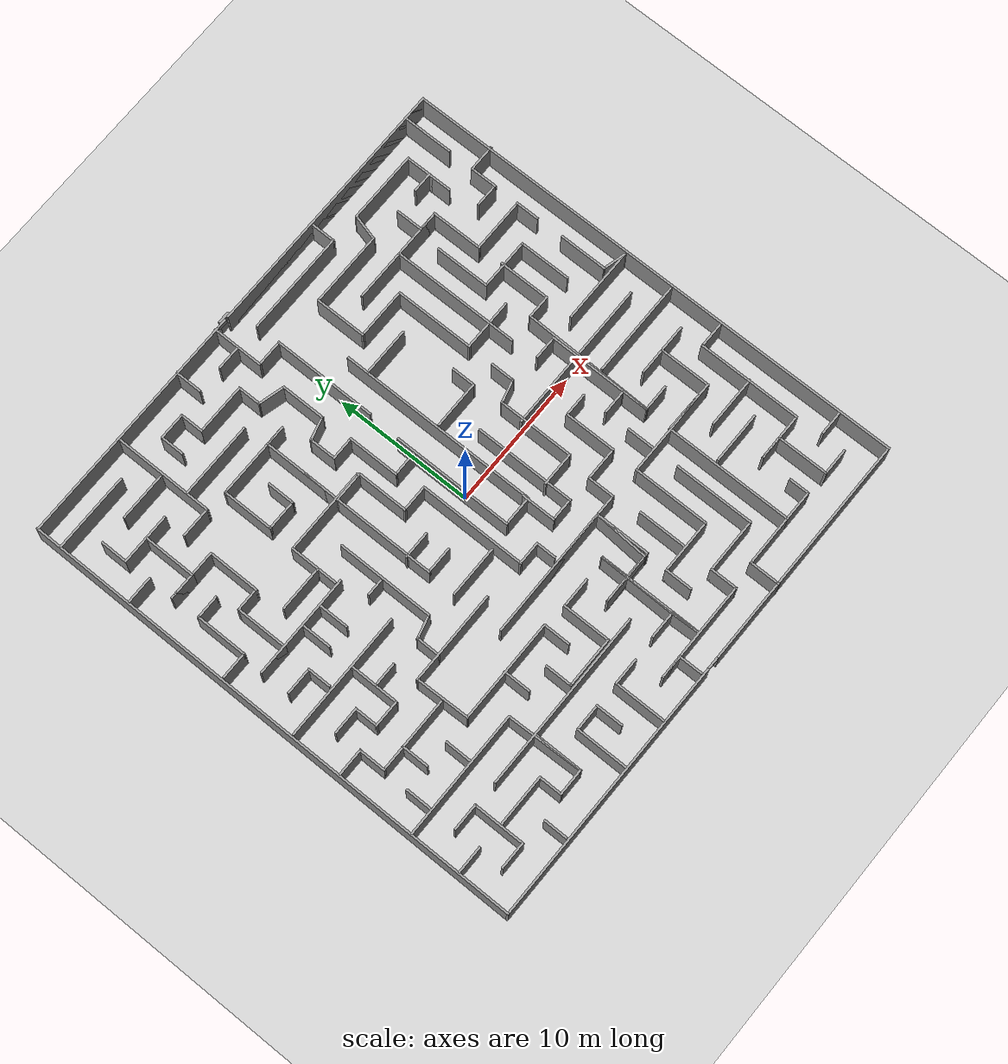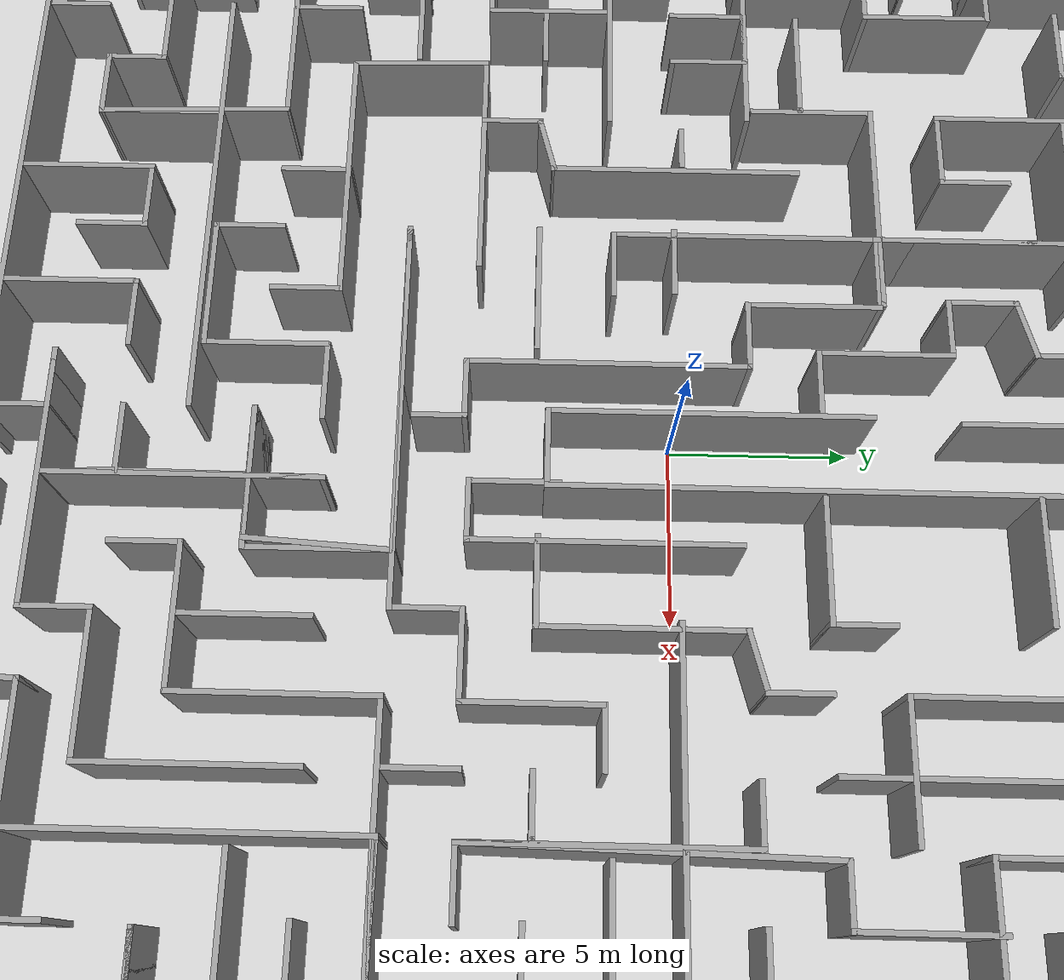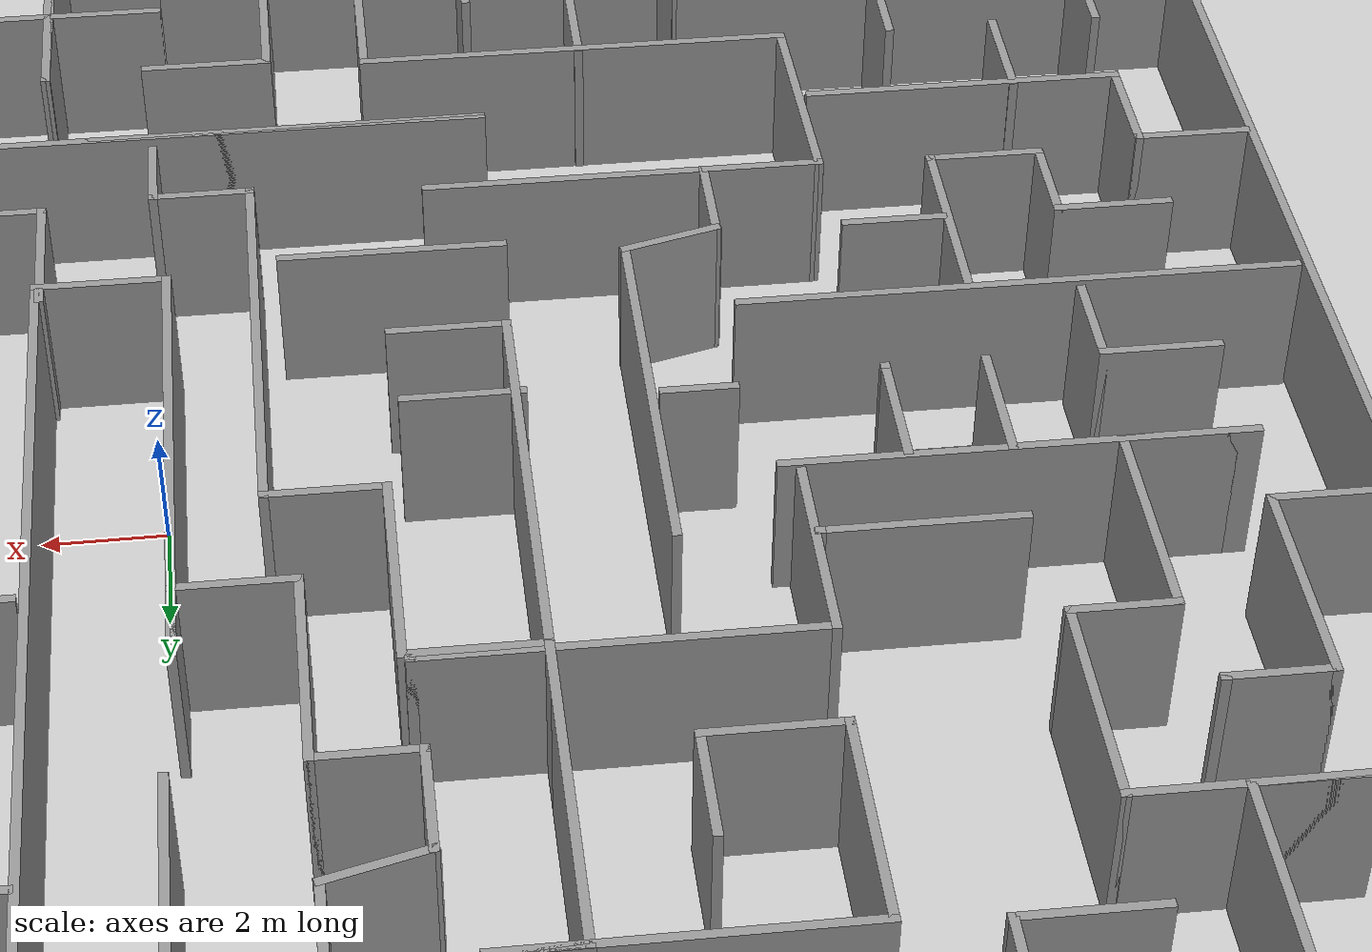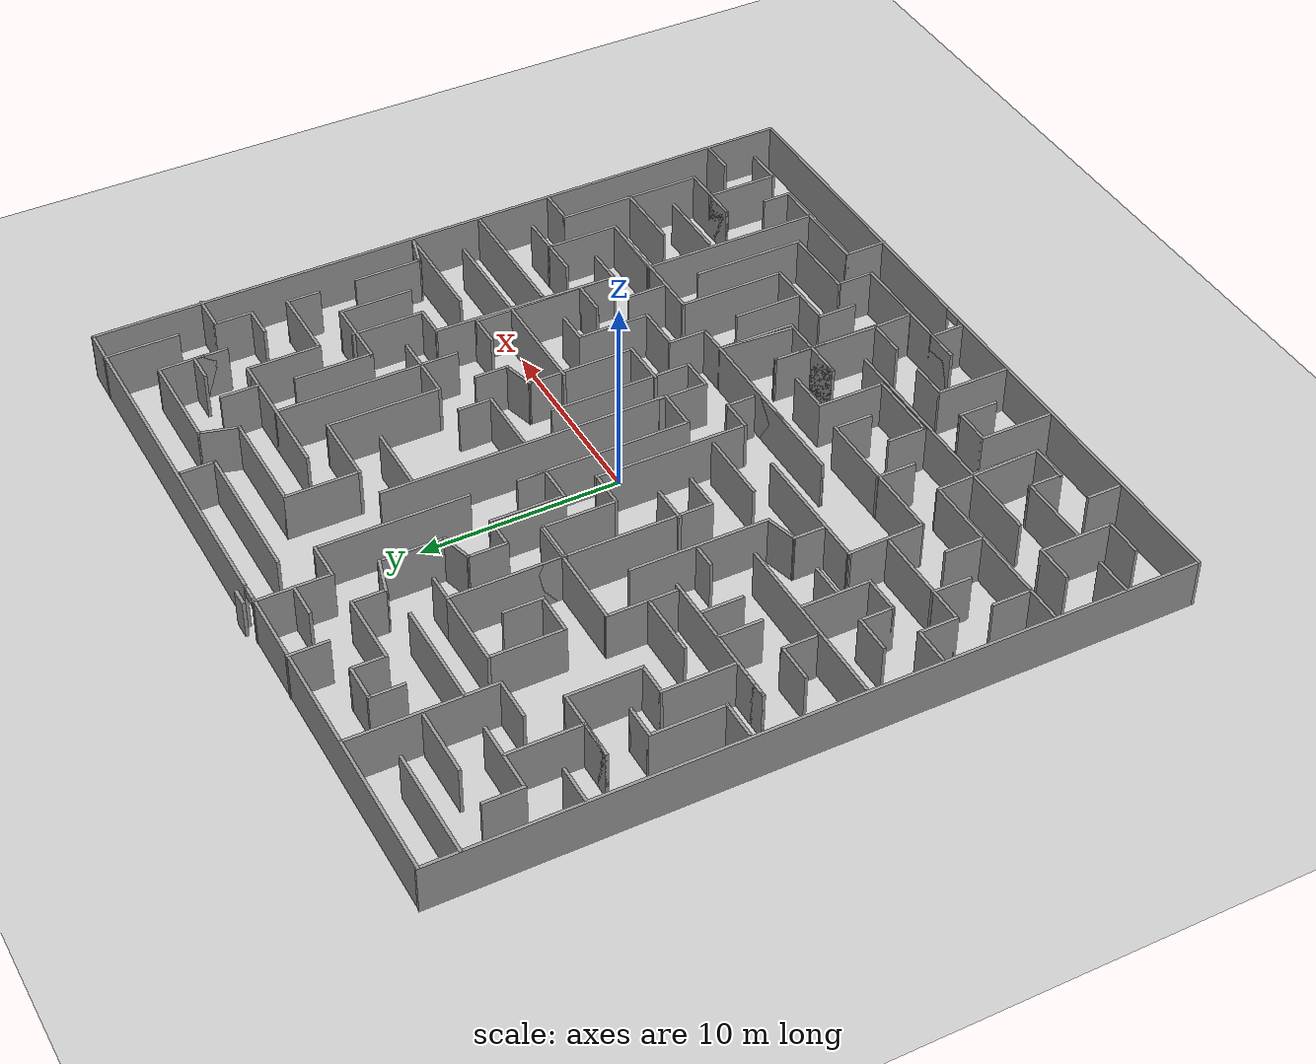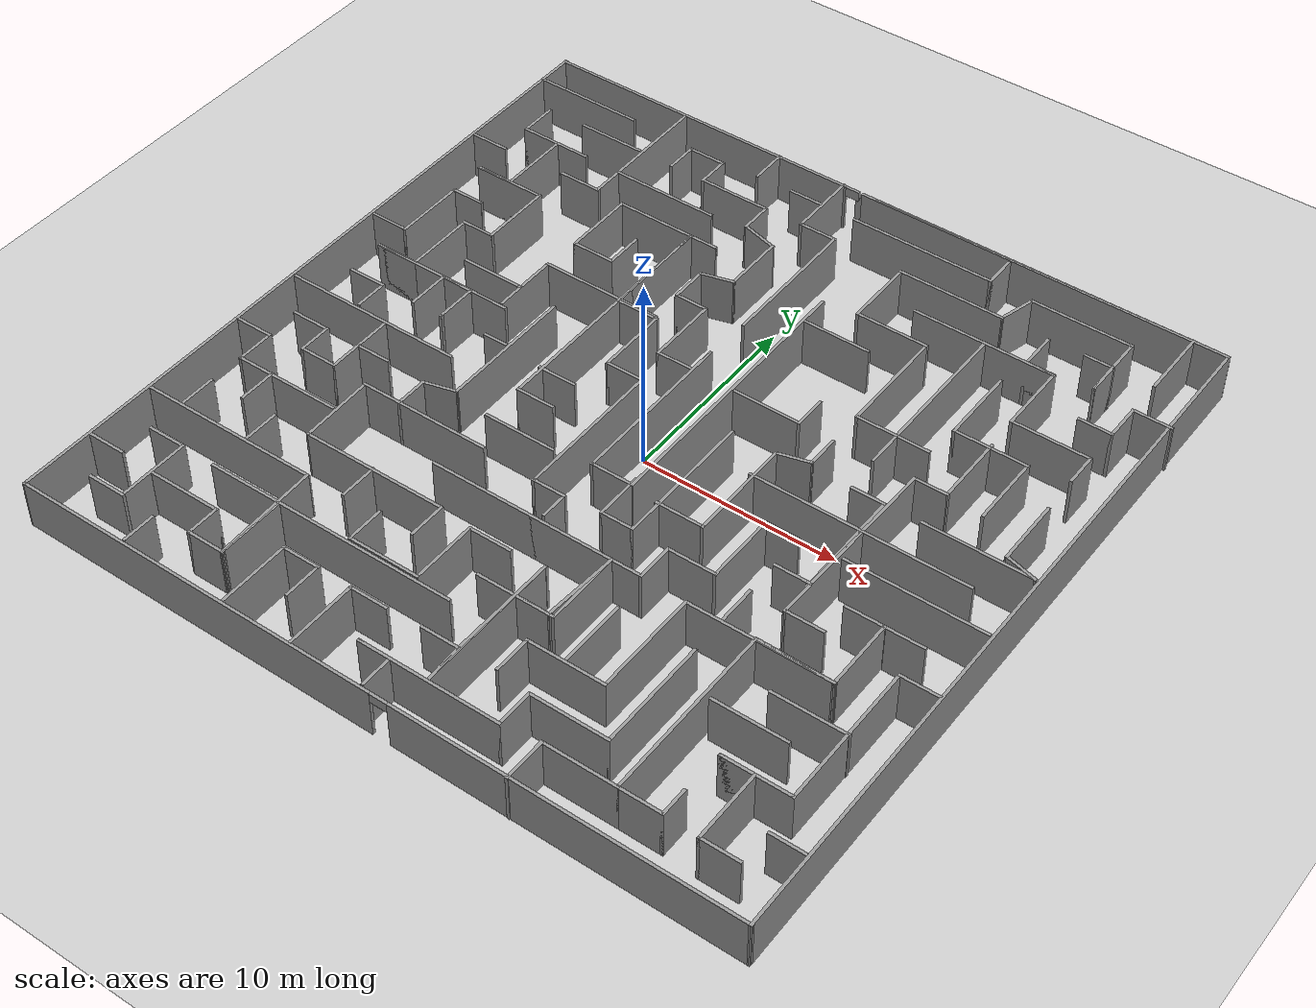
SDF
<sdf version="1.7">
 <world name="default">
  <light name="sun" type="directional">
   <pose>0 0 10 0 -0 0</pose>
   <diffuse>0.8 0.8 0.8 1</diffuse>
   <specular>0.2 0.2 0.2 1</specular>
   <attenuation>
    <range>1000</range>
    <constant>0.9</constant>
    <linear>0.01</linear>
    <quadratic>0.001</quadratic>
   </attenuation>
   <direction>-0.5 0.1 -0.9</direction>
   <spot><inner_angle>0</inner_angle><outer_angle>0</outer_angle><falloff>0</falloff></spot>
  </light>
  <model name="ground_plane">
   <static>1</static>
   <link name="link">
    <collision name="collision">
     <geometry><plane><normal>0 0 1</normal><size>100 100</size></plane></geometry>
     <surface>
      <contact><collide_bitmask>65535</collide_bitmask></contact>
      <friction><ode><mu>100</mu><mu2>50</mu2></ode></friction>
     </surface>
    </collision>
    <visual name="visual">
     <cast_shadows>0</cast_shadows>
     <geometry><plane><normal>0 0 1</normal><size>100 100</size></plane></geometry>
     <material>
      <script><uri>file://media/materials/scripts/gazebo.material</uri><name>Gazebo/Grey</name></script>
     </material>
    </visual>
   </link>
  </model>
  <gravity>0 0 -9.8</gravity>
  <magnetic_field>6e-06 2.3e-05 -4.2e-05</magnetic_field>
  <atmosphere type="adiabatic"/>
  <physics type="ode">
   <max_step_size>0.001</max_step_size>
   <real_time_factor>1</real_time_factor>
   <real_time_update_rate>1000</real_time_update_rate>
  </physics>
  <scene><ambient>0.4 0.4 0.4 1</ambient><background>0.7 0.7 0.7 1</background><shadows>1</shadows></scene>
  <audio><device>default</device></audio>
  <spherical_coordinates>
   <surface_model>EARTH_WGS84</surface_model>
   <latitude_deg>0</latitude_deg>
   <longitude_deg>0</longitude_deg>
   <elevation>0</elevation>
   <heading_deg>0</heading_deg>
  </spherical_coordinates>
  <model name="maze">
   <pose>-0.086607 -0.007324 0 0 -0 0</pose>
   <link name="Door_0">
    <collision name="Door_0_Collision">
     <geometry><box><size>0.9 0.17 2</size></box></geometry>
     <pose>0 0 1 0 -0 0</pose>
    </collision>
    <visual name="Door_0_Visual">
     <pose>0 0 1 0 -0 0</pose>
     <geometry><box><size>0.9 0.17 2</size></box></geometry>
     <material>
      <script><uri>file://media/materials/scripts/gazebo.material</uri><name>Gazebo/Grey</name></script>
     </material>
    </visual>
    <pose>-0.791347 18.8153 0 0 -0 0</pose>
   </link>
   <link name="Wall_1">
    <pose>-0.020115 18.5034 0 0 -0 0</pose>
    <visual name="Wall_1_Visual_0">
     <pose>-10.0629 0 1.25 0 -0 0</pose>
     <geometry><box><size>16.8742 0.15 2.5</size></box></geometry>
     <material>
      <script><uri>file://media/materials/scripts/gazebo.material</uri><name>Gazebo/Grey</name></script>
      <ambient>1 1 1 1</ambient>
     </material>
     <meta><layer>0</layer></meta>
    </visual>
    <collision name="Wall_1_Collision_0">
     <geometry><box><size>16.8742 0.15 2.5</size></box></geometry>
     <pose>-10.0629 0 1.25 0 -0 0</pose>
    </collision>
    <visual name="Wall_1_Visual_1">
     <pose>8.88711 0 1.25 0 -0 0</pose>
     <geometry><box><size>19.2258 0.15 2.5</size></box></geometry>
     <material>
      <script><uri>file://media/materials/scripts/gazebo.material</uri><name>Gazebo/Grey</name></script>
      <ambient>1 1 1 1</ambient>
     </material>
     <meta><layer>0</layer></meta>
    </visual>
    <collision name="Wall_1_Collision_1">
     <geometry><box><size>19.2258 0.15 2.5</size></box></geometry>
     <pose>8.88711 0 1.25 0 -0 0</pose>
    </collision>
    <visual name="Wall_1_Visual_2">
     <pose>9.25121 0 1.25 0 -0 0</pose>
     <geometry><box><size>18.4976 0.15 2.5</size></box></geometry>
     <material>
      <script><uri>file://media/materials/scripts/gazebo.material</uri><name>Gazebo/Grey</name></script>
      <ambient>1 1 1 1</ambient>
     </material>
     <meta><layer>0</layer></meta>
    </visual>
    <collision name="Wall_1_Collision_2">
     <geometry><box><size>18.4976 0.15 2.5</size></box></geometry>
     <pose>9.25121 0 1.25 0 -0 0</pose>
    </collision>
    <visual name="Wall_1_Visual_3">
     <pose>-1.26169 0 2.25 0 -0 0</pose>
     <geometry><box><size>0.7282 0.15 0.5</size></box></geometry>
     <material>
      <script><uri>file://media/materials/scripts/gazebo.material</uri><name>Gazebo/Grey</name></script>
      <ambient>1 1 1 1</ambient>
     </material>
     <meta><layer>0</layer></meta>
    </visual>
    <collision name="Wall_1_Collision_3">
     <geometry><box><size>0.7282 0.15 0.5</size></box></geometry>
     <pose>-1.26169 0 2.25 0 -0 0</pose>
    </collision>
   </link>
   <link name="Wall_100">
    <collision name="Wall_100_Collision">
     <geometry><box><size>9.5 0.15 2.5</size></box></geometry>
     <pose>0 0 1.25 0 -0 0</pose>
    </collision>
    <visual name="Wall_100_Visual">
     <pose>0 0 1.25 0 -0 0</pose>
     <geometry><box><size>9.5 0.15 2.5</size></box></geometry>
     <material>
      <script><uri>file://media/materials/scripts/gazebo.material</uri><name>Gazebo/Grey</name></script>
      <ambient>1 1 1 1</ambient>
     </material>
     <meta><layer>0</layer></meta>
    </visual>
    <pose>-0.81592 -7.32874 0 0 -0 3.14159</pose>
   </link>
   <link name="Wall_102">
    <collision name="Wall_102_Collision">
     <geometry><box><size>2 0.15 2.5</size></box></geometry>
     <pose>0 0 1.25 0 -0 0</pose>
    </collision>
    <visual name="Wall_102_Visual">
     <pose>0 0 1.25 0 -0 0</pose>
     <geometry><box><size>2 0.15 2.5</size></box></geometry>
     <material>
      <script><uri>file://media/materials/scripts/gazebo.material</uri><name>Gazebo/Grey</name></script>
      <ambient>1 1 1 1</ambient>
     </material>
     <meta><layer>0</layer></meta>
    </visual>
    <pose>-5.49649 -11.7996 0 0 -0 -1.5708</pose>
   </link>
   <link name="Wall_103">
    <collision name="Wall_103_Collision">
     <geometry><box><size>3.75 0.15 2.5</size></box></geometry>
     <pose>0 0 1.25 0 -0 0</pose>
    </collision>
    <visual name="Wall_103_Visual">
     <pose>0 0 1.25 0 -0 0</pose>
     <geometry><box><size>3.75 0.15 2.5</size></box></geometry>
     <material>
      <script><uri>file://media/materials/scripts/gazebo.material</uri><name>Gazebo/Grey</name></script>
      <ambient>1 1 1 1</ambient>
     </material>
     <meta><layer>0</layer></meta>
    </visual>
    <pose>-3.69649 -12.7246 0 0 -0 0</pose>
   </link>
   <link name="Wall_104">
    <collision name="Wall_104_Collision">
     <geometry><box><size>3.5 0.15 2.5</size></box></geometry>
     <pose>0 0 1.25 0 -0 0</pose>
    </collision>
    <visual name="Wall_104_Visual">
     <pose>0 0 1.25 0 -0 0</pose>
     <geometry><box><size>3.5 0.15 2.5</size></box></geometry>
     <material>
      <script><uri>file://media/materials/scripts/gazebo.material</uri><name>Gazebo/Grey</name></script>
      <ambient>1 1 1 1</ambient>
     </material>
     <meta><layer>0</layer></meta>
    </visual>
    <pose>-1.89649 -11.0496 0 0 -0 1.5708</pose>
   </link>
   <link name="Wall_105">
    <collision name="Wall_105_Collision">
     <geometry><box><size>2.25 0.15 2.5</size></box></geometry>
     <pose>0 0 1.25 0 -0 0</pose>
    </collision>
    <visual name="Wall_105_Visual">
     <pose>0 0 1.25 0 -0 0</pose>
     <geometry><box><size>2.25 0.15 2.5</size></box></geometry>
     <material>
      <script><uri>file://media/materials/scripts/gazebo.material</uri><name>Gazebo/Grey</name></script>
      <ambient>1 1 1 1</ambient>
     </material>
     <meta><layer>0</layer></meta>
    </visual>
    <pose>-0.846487 -9.37457 0 0 -0 0</pose>
   </link>
   <link name="Wall_107">
    <collision name="Wall_107_Collision">
     <geometry><box><size>1.5 0.15 2.5</size></box></geometry>
     <pose>0 0 1.25 0 -0 0</pose>
    </collision>
    <visual name="Wall_107_Visual">
     <pose>0 0 1.25 0 -0 0</pose>
     <geometry><box><size>1.5 0.15 2.5</size></box></geometry>
     <material>
      <script><uri>file://media/materials/scripts/gazebo.material</uri><name>Gazebo/Grey</name></script>
      <ambient>1 1 1 1</ambient>
     </material>
     <meta><layer>0</layer></meta>
    </visual>
    <pose>0.093707 -6.29433 0 0 -0 1.5708</pose>
   </link>
   <link name="Wall_108">
    <collision name="Wall_108_Collision">
     <geometry><box><size>1.75 0.15 2.5</size></box></geometry>
     <pose>0 0 1.25 0 -0 0</pose>
    </collision>
    <visual name="Wall_108_Visual">
     <pose>0 0 1.25 0 -0 0</pose>
     <geometry><box><size>1.75 0.15 2.5</size></box></geometry>
     <material>
      <script><uri>file://media/materials/scripts/gazebo.material</uri><name>Gazebo/Grey</name></script>
      <ambient>1 1 1 1</ambient>
     </material>
     <meta><layer>0</layer></meta>
    </visual>
    <pose>-0.706293 -5.61933 0 0 -0 3.14159</pose>
   </link>
   <link name="Wall_109">
    <collision name="Wall_109_Collision">
     <geometry><box><size>7.75 0.15 2.5</size></box></geometry>
     <pose>0 0 1.25 0 -0 0</pose>
    </collision>
    <visual name="Wall_109_Visual">
     <pose>0 0 1.25 0 -0 0</pose>
     <geometry><box><size>7.75 0.15 2.5</size></box></geometry>
     <material>
      <script><uri>file://media/materials/scripts/gazebo.material</uri><name>Gazebo/Grey</name></script>
      <ambient>1 1 1 1</ambient>
     </material>
     <meta><layer>0</layer></meta>
    </visual>
    <pose>-1.50629 -1.81933 0 0 -0 1.5708</pose>
   </link>
   <link name="Wall_11">
    <collision name="Wall_11_Collision">
     <geometry><box><size>3.75 0.15 2.5</size></box></geometry>
     <pose>0 0 1.25 0 -0 0</pose>
    </collision>
    <visual name="Wall_11_Visual">
     <pose>0 0 1.25 0 -0 0</pose>
     <geometry><box><size>3.75 0.15 2.5</size></box></geometry>
     <material>
      <script><uri>file://media/materials/scripts/gazebo.material</uri><name>Gazebo/Grey</name></script>
      <ambient>1 1 1 1</ambient>
     </material>
     <meta><layer>0</layer></meta>
    </visual>
    <pose>-14.6968 11.1408 0 0 -0 -1.5708</pose>
   </link>
   <link name="Wall_110">
    <collision name="Wall_110_Collision">
     <geometry><box><size>2 0.15 2.5</size></box></geometry>
     <pose>0 0 1.25 0 -0 0</pose>
    </collision>
    <visual name="Wall_110_Visual">
     <pose>0 0 1.25 0 -0 0</pose>
     <geometry><box><size>2 0.15 2.5</size></box></geometry>
     <material>
      <script><uri>file://media/materials/scripts/gazebo.material</uri><name>Gazebo/Grey</name></script>
      <ambient>1 1 1 1</ambient>
     </material>
     <meta><layer>0</layer></meta>
    </visual>
    <pose>-2.43129 1.98067 0 0 -0 3.14159</pose>
   </link>
   <link name="Wall_111">
    <collision name="Wall_111_Collision">
     <geometry><box><size>3.75 0.15 2.5</size></box></geometry>
     <pose>0 0 1.25 0 -0 0</pose>
    </collision>
    <visual name="Wall_111_Visual">
     <pose>0 0 1.25 0 -0 0</pose>
     <geometry><box><size>3.75 0.15 2.5</size></box></geometry>
     <material>
      <script><uri>file://media/materials/scripts/gazebo.material</uri><name>Gazebo/Grey</name></script>
      <ambient>1 1 1 1</ambient>
     </material>
     <meta><layer>0</layer></meta>
    </visual>
    <pose>-3.35629 3.78067 0 0 -0 1.5708</pose>
   </link>
   <link name="Wall_112">
    <collision name="Wall_112_Collision">
     <geometry><box><size>2.25 0.15 2.5</size></box></geometry>
     <pose>0 0 1.25 0 -0 0</pose>
    </collision>
    <visual name="Wall_112_Visual">
     <pose>0 0 1.25 0 -0 0</pose>
     <geometry><box><size>2.25 0.15 2.5</size></box></geometry>
     <material>
      <script><uri>file://media/materials/scripts/gazebo.material</uri><name>Gazebo/Grey</name></script>
      <ambient>1 1 1 1</ambient>
     </material>
     <meta><layer>0</layer></meta>
    </visual>
    <pose>-4.40629 5.58067 0 0 -0 3.14159</pose>
   </link>
   <link name="Wall_113">
    <collision name="Wall_113_Collision">
     <geometry><box><size>5.75 0.15 2.5</size></box></geometry>
     <pose>0 0 1.25 0 -0 0</pose>
    </collision>
    <visual name="Wall_113_Visual">
     <pose>0 0 1.25 0 -0 0</pose>
     <geometry><box><size>5.75 0.15 2.5</size></box></geometry>
     <material>
      <script><uri>file://media/materials/scripts/gazebo.material</uri><name>Gazebo/Grey</name></script>
      <ambient>1 1 1 1</ambient>
     </material>
     <meta><layer>0</layer></meta>
    </visual>
    <pose>-5.45629 8.38067 0 0 -0 1.5708</pose>
   </link>
   <link name="Wall_114">
    <collision name="Wall_114_Collision">
     <geometry><box><size>1.5 0.15 2.5</size></box></geometry>
     <pose>0 0 1.25 0 -0 0</pose>
    </collision>
    <visual name="Wall_114_Visual">
     <pose>0 0 1.25 0 -0 0</pose>
     <geometry><box><size>1.5 0.15 2.5</size></box></geometry>
     <material>
      <script><uri>file://media/materials/scripts/gazebo.material</uri><name>Gazebo/Grey</name></script>
      <ambient>1 1 1 1</ambient>
     </material>
     <meta><layer>0</layer></meta>
    </visual>
    <pose>-4.78129 11.1807 0 0 -0 0</pose>
   </link>
   <link name="Wall_115">
    <collision name="Wall_115_Collision">
     <geometry><box><size>5.5 0.15 2.5</size></box></geometry>
     <pose>0 0 1.25 0 -0 0</pose>
    </collision>
    <visual name="Wall_115_Visual">
     <pose>0 0 1.25 0 -0 0</pose>
     <geometry><box><size>5.5 0.15 2.5</size></box></geometry>
     <material>
      <script><uri>file://media/materials/scripts/gazebo.material</uri><name>Gazebo/Grey</name></script>
      <ambient>1 1 1 1</ambient>
     </material>
     <meta><layer>0</layer></meta>
    </visual>
    <pose>-6.78129 11.1807 0 0 -0 3.14159</pose>
   </link>
   <link name="Wall_116">
    <collision name="Wall_116_Collision">
     <geometry><box><size>3.75 0.15 2.5</size></box></geometry>
     <pose>0 0 1.25 0 -0 0</pose>
    </collision>
    <visual name="Wall_116_Visual">
     <pose>0 0 1.25 0 -0 0</pose>
     <geometry><box><size>3.75 0.15 2.5</size></box></geometry>
     <material>
      <script><uri>file://media/materials/scripts/gazebo.material</uri><name>Gazebo/Grey</name></script>
      <ambient>1 1 1 1</ambient>
     </material>
     <meta><layer>0</layer></meta>
    </visual>
    <pose>-9.45629 9.38067 0 0 -0 -1.5708</pose>
   </link>
   <link name="Wall_117">
    <collision name="Wall_117_Collision">
     <geometry><box><size>2.25 0.15 2.5</size></box></geometry>
     <pose>0 0 1.25 0 -0 0</pose>
    </collision>
    <visual name="Wall_117_Visual">
     <pose>0 0 1.25 0 -0 0</pose>
     <geometry><box><size>2.25 0.15 2.5</size></box></geometry>
     <material>
      <script><uri>file://media/materials/scripts/gazebo.material</uri><name>Gazebo/Grey</name></script>
      <ambient>1 1 1 1</ambient>
     </material>
     <meta><layer>0</layer></meta>
    </visual>
    <pose>-8.40629 7.58067 0 0 -0 0</pose>
   </link>
   <link name="Wall_118">
    <collision name="Wall_118_Collision">
     <geometry><box><size>2 0.15 2.5</size></box></geometry>
     <pose>0 0 1.25 0 -0 0</pose>
    </collision>
    <visual name="Wall_118_Visual">
     <pose>0 0 1.25 0 -0 0</pose>
     <geometry><box><size>2 0.15 2.5</size></box></geometry>
     <material>
      <script><uri>file://media/materials/scripts/gazebo.material</uri><name>Gazebo/Grey</name></script>
      <ambient>1 1 1 1</ambient>
     </material>
     <meta><layer>0</layer></meta>
    </visual>
    <pose>-7.35629 8.50567 0 0 -0 1.5708</pose>
   </link>
   <link name="Wall_12">
    <collision name="Wall_12_Collision">
     <geometry><box><size>2 0.15 2.5</size></box></geometry>
     <pose>0 0 1.25 0 -0 0</pose>
    </collision>
    <visual name="Wall_12_Visual">
     <pose>0 0 1.25 0 -0 0</pose>
     <geometry><box><size>2 0.15 2.5</size></box></geometry>
     <material>
      <script><uri>file://media/materials/scripts/gazebo.material</uri><name>Gazebo/Grey</name></script>
      <ambient>1 1 1 1</ambient>
     </material>
     <meta><layer>0</layer></meta>
    </visual>
    <pose>-15.6218 9.34077 0 0 -0 3.14159</pose>
   </link>
   <link name="Wall_120">
    <collision name="Wall_120_Collision">
     <geometry><box><size>6.75 0.15 2.5</size></box></geometry>
     <pose>0 0 1.25 0 -0 0</pose>
    </collision>
    <visual name="Wall_120_Visual">
     <pose>0 0 1.25 0 -0 0</pose>
     <geometry><box><size>6.75 0.15 2.5</size></box></geometry>
     <material>
      <script><uri>file://media/materials/scripts/gazebo.material</uri><name>Gazebo/Grey</name></script>
      <ambient>1 1 1 1</ambient>
     </material>
     <meta><layer>0</layer></meta>
    </visual>
    <pose>-7.73365 -5.37864 0 0 -0 3.14159</pose>
   </link>
   <link name="Wall_121">
    <collision name="Wall_121_Collision">
     <geometry><box><size>3.94367 0.15 2.5</size></box></geometry>
     <pose>0 0 1.25 0 -0 0</pose>
    </collision>
    <visual name="Wall_121_Visual">
     <pose>0 0 1.25 0 -0 0</pose>
     <geometry><box><size>3.94367 0.15 2.5</size></box></geometry>
     <material>
      <script><uri>file://media/materials/scripts/gazebo.material</uri><name>Gazebo/Grey</name></script>
      <ambient>1 1 1 1</ambient>
     </material>
     <meta><layer>0</layer></meta>
    </visual>
    <pose>-10.9874 -7.27492 0 0 -0 -1.54643</pose>
   </link>
   <link name="Wall_123">
    <collision name="Wall_123_Collision">
     <geometry><box><size>1.75 0.15 2.5</size></box></geometry>
     <pose>0 0 1.25 0 -0 0</pose>
    </collision>
    <visual name="Wall_123_Visual">
     <pose>0 0 1.25 0 -0 0</pose>
     <geometry><box><size>1.75 0.15 2.5</size></box></geometry>
     <material>
      <script><uri>file://media/materials/scripts/gazebo.material</uri><name>Gazebo/Grey</name></script>
      <ambient>1 1 1 1</ambient>
     </material>
     <meta><layer>0</layer></meta>
    </visual>
    <pose>-9.08336 -4.57864 0 0 -0 1.5708</pose>
   </link>
   <link name="Wall_124">
    <collision name="Wall_124_Collision">
     <geometry><box><size>1.75 0.15 2.5</size></box></geometry>
     <pose>0 0 1.25 0 -0 0</pose>
    </collision>
    <visual name="Wall_124_Visual">
     <pose>0 0 1.25 0 -0 0</pose>
     <geometry><box><size>1.75 0.15 2.5</size></box></geometry>
     <material>
      <script><uri>file://media/materials/scripts/gazebo.material</uri><name>Gazebo/Grey</name></script>
      <ambient>1 1 1 1</ambient>
     </material>
     <meta><layer>0</layer></meta>
    </visual>
    <pose>-8.31062 -3.57159 0 0 -0 0.261799</pose>
   </link>
   <link name="Wall_125">
    <collision name="Wall_125_Collision">
     <geometry><box><size>7 0.15 2.5</size></box></geometry>
     <pose>0 0 1.25 0 -0 0</pose>
    </collision>
    <visual name="Wall_125_Visual">
     <pose>0 0 1.25 0 -0 0</pose>
     <geometry><box><size>7 0.15 2.5</size></box></geometry>
     <material>
      <script><uri>file://media/materials/scripts/gazebo.material</uri><name>Gazebo/Grey</name></script>
      <ambient>1 1 1 1</ambient>
     </material>
     <meta><layer>0</layer></meta>
    </visual>
    <pose>-7.53788 0.060469 0 0 -0 1.5708</pose>
   </link>
   <link name="Wall_127">
    <collision name="Wall_127_Collision">
     <geometry><box><size>1.25 0.15 2.5</size></box></geometry>
     <pose>0 0 1.25 0 -0 0</pose>
    </collision>
    <visual name="Wall_127_Visual">
     <pose>0 0 1.25 0 -0 0</pose>
     <geometry><box><size>1.25 0.15 2.5</size></box></geometry>
     <material>
      <script><uri>file://media/materials/scripts/gazebo.material</uri><name>Gazebo/Grey</name></script>
      <ambient>1 1 1 1</ambient>
     </material>
     <meta><layer>0</layer></meta>
    </visual>
    <pose>-8.28864 0.24996 0 0 -0 0</pose>
   </link>
   <link name="Wall_13">
    <collision name="Wall_13_Collision">
     <geometry><box><size>3.75 0.15 2.5</size></box></geometry>
     <pose>0 0 1.25 0 -0 0</pose>
    </collision>
    <visual name="Wall_13_Visual">
     <pose>0 0 1.25 0 -0 0</pose>
     <geometry><box><size>3.75 0.15 2.5</size></box></geometry>
     <material>
      <script><uri>file://media/materials/scripts/gazebo.material</uri><name>Gazebo/Grey</name></script>
      <ambient>1 1 1 1</ambient>
     </material>
     <meta><layer>0</layer></meta>
    </visual>
    <pose>-14.7468 9.34077 0 0 -0 0</pose>
   </link>
   <link name="Wall_130">
    <collision name="Wall_130_Collision">
     <geometry><box><size>3.5 0.15 2.5</size></box></geometry>
     <pose>0 0 1.25 0 -0 0</pose>
    </collision>
    <visual name="Wall_130_Visual">
     <pose>0 0 1.25 0 -0 0</pose>
     <geometry><box><size>3.5 0.15 2.5</size></box></geometry>
     <material>
      <script><uri>file://media/materials/scripts/gazebo.material</uri><name>Gazebo/Grey</name></script>
      <ambient>1 1 1 1</ambient>
     </material>
     <meta><layer>0</layer></meta>
    </visual>
    <pose>-9.57281 4.0051 0 0 -0 1.5708</pose>
   </link>
   <link name="Wall_131">
    <collision name="Wall_131_Collision">
     <geometry><box><size>6.25 0.15 2.5</size></box></geometry>
     <pose>0 0 1.25 0 -0 0</pose>
    </collision>
    <visual name="Wall_131_Visual">
     <pose>0 0 1.25 0 -0 0</pose>
     <geometry><box><size>6.25 0.15 2.5</size></box></geometry>
     <material>
      <script><uri>file://media/materials/scripts/gazebo.material</uri><name>Gazebo/Grey</name></script>
      <ambient>1 1 1 1</ambient>
     </material>
     <meta><layer>0</layer></meta>
    </visual>
    <pose>-6.5228 5.6801 0 0 -0 0</pose>
   </link>
   <link name="Wall_132">
    <collision name="Wall_132_Collision">
     <geometry><box><size>0.16 0.15 2.5</size></box></geometry>
     <pose>0 0 1.25 0 -0 0</pose>
    </collision>
    <visual name="Wall_132_Visual">
     <pose>0 0 1.25 0 -0 0</pose>
     <geometry><box><size>0.16 0.15 2.5</size></box></geometry>
     <material>
      <script><uri>file://media/materials/scripts/gazebo.material</uri><name>Gazebo/Grey</name></script>
      <ambient>1 1 1 1</ambient>
     </material>
     <meta><layer>0</layer></meta>
    </visual>
    <pose>-3.4678 5.6801 0 0 -0 0</pose>
   </link>
   <link name="Wall_134">
    <collision name="Wall_134_Collision">
     <geometry><box><size>3.25 0.15 2.5</size></box></geometry>
     <pose>0 0 1.25 0 -0 0</pose>
    </collision>
    <visual name="Wall_134_Visual">
     <pose>0 0 1.25 0 -0 0</pose>
     <geometry><box><size>3.25 0.15 2.5</size></box></geometry>
     <material>
      <script><uri>file://media/materials/scripts/gazebo.material</uri><name>Gazebo/Grey</name></script>
      <ambient>1 1 1 1</ambient>
     </material>
     <meta><layer>0</layer></meta>
    </visual>
    <pose>-11.2042 3.67607 0 0 -0 0</pose>
   </link>
   <link name="Wall_135">
    <collision name="Wall_135_Collision">
     <geometry><box><size>0.16 0.15 2.5</size></box></geometry>
     <pose>0 0 1.25 0 -0 0</pose>
    </collision>
    <visual name="Wall_135_Visual">
     <pose>0 0 1.25 0 -0 0</pose>
     <geometry><box><size>0.16 0.15 2.5</size></box></geometry>
     <material>
      <script><uri>file://media/materials/scripts/gazebo.material</uri><name>Gazebo/Grey</name></script>
      <ambient>1 1 1 1</ambient>
     </material>
     <meta><layer>0</layer></meta>
    </visual>
    <pose>-9.64919 3.67607 0 0 -0 0</pose>
   </link>
   <link name="Wall_136">
    <collision name="Wall_136_Collision">
     <geometry><box><size>0.16 0.15 2.5</size></box></geometry>
     <pose>0 0 1.25 0 -0 0</pose>
    </collision>
    <visual name="Wall_136_Visual">
     <pose>0 0 1.25 0 -0 0</pose>
     <geometry><box><size>0.16 0.15 2.5</size></box></geometry>
     <material>
      <script><uri>file://media/materials/scripts/gazebo.material</uri><name>Gazebo/Grey</name></script>
      <ambient>1 1 1 1</ambient>
     </material>
     <meta><layer>0</layer></meta>
    </visual>
    <pose>-9.63919 3.67607 0 0 -0 0</pose>
   </link>
   <link name="Wall_138">
    <collision name="Wall_138_Collision">
     <geometry><box><size>7.25 0.15 2.5</size></box></geometry>
     <pose>0 0 1.25 0 -0 0</pose>
    </collision>
    <visual name="Wall_138_Visual">
     <pose>0 0 1.25 0 -0 0</pose>
     <geometry><box><size>7.25 0.15 2.5</size></box></geometry>
     <material>
      <script><uri>file://media/materials/scripts/gazebo.material</uri><name>Gazebo/Grey</name></script>
      <ambient>1 1 1 1</ambient>
     </material>
     <meta><layer>0</layer></meta>
    </visual>
    <pose>-11.002 14.8809 0 0 -0 -1.5708</pose>
   </link>
   <link name="Wall_139">
    <collision name="Wall_139_Collision">
     <geometry><box><size>2.25 0.15 2.5</size></box></geometry>
     <pose>0 0 1.25 0 -0 0</pose>
    </collision>
    <visual name="Wall_139_Visual">
     <pose>0 0 1.25 0 -0 0</pose>
     <geometry><box><size>2.25 0.15 2.5</size></box></geometry>
     <material>
      <script><uri>file://media/materials/scripts/gazebo.material</uri><name>Gazebo/Grey</name></script>
      <ambient>1 1 1 1</ambient>
     </material>
     <meta><layer>0</layer></meta>
    </visual>
    <pose>-12.052 11.3309 0 0 -0 3.14159</pose>
   </link>
   <link name="Wall_14">
    <collision name="Wall_14_Collision">
     <geometry><box><size>3.75 0.15 2.5</size></box></geometry>
     <pose>0 0 1.25 0 -0 0</pose>
    </collision>
    <visual name="Wall_14_Visual">
     <pose>0 0 1.25 0 -0 0</pose>
     <geometry><box><size>3.75 0.15 2.5</size></box></geometry>
     <material>
      <script><uri>file://media/materials/scripts/gazebo.material</uri><name>Gazebo/Grey</name></script>
      <ambient>1 1 1 1</ambient>
     </material>
     <meta><layer>0</layer></meta>
    </visual>
    <pose>-12.9468 7.54077 0 0 -0 -1.5708</pose>
   </link>
   <link name="Wall_141">
    <collision name="Wall_141_Collision">
     <geometry><box><size>5.5 0.15 2.5</size></box></geometry>
     <pose>0 0 1.25 0 -0 0</pose>
    </collision>
    <visual name="Wall_141_Visual">
     <pose>0 0 1.25 0 -0 0</pose>
     <geometry><box><size>5.5 0.15 2.5</size></box></geometry>
     <material>
      <script><uri>file://media/materials/scripts/gazebo.material</uri><name>Gazebo/Grey</name></script>
      <ambient>1 1 1 1</ambient>
     </material>
     <meta><layer>0</layer></meta>
    </visual>
    <pose>-8.28079 12.9721 0 0 -0 0</pose>
   </link>
   <link name="Wall_143">
    <collision name="Wall_143_Collision">
     <geometry><box><size>3.5 0.15 2.5</size></box></geometry>
     <pose>0 0 1.25 0 -0 0</pose>
    </collision>
    <visual name="Wall_143_Visual">
     <pose>0 0 1.25 0 -0 0</pose>
     <geometry><box><size>3.5 0.15 2.5</size></box></geometry>
     <material>
      <script><uri>file://media/materials/scripts/gazebo.material</uri><name>Gazebo/Grey</name></script>
      <ambient>1 1 1 1</ambient>
     </material>
     <meta><layer>0</layer></meta>
    </visual>
    <pose>-12.8892 14.9151 0 0 -0 0</pose>
   </link>
   <link name="Wall_145">
    <collision name="Wall_145_Collision">
     <geometry><box><size>5.71184 0.15 2.5</size></box></geometry>
     <pose>0 0 1.25 0 -0 0</pose>
    </collision>
    <visual name="Wall_145_Visual">
     <pose>0 0 1.25 0 -0 0</pose>
     <geometry><box><size>5.71184 0.15 2.5</size></box></geometry>
     <material>
      <script><uri>file://media/materials/scripts/gazebo.material</uri><name>Gazebo/Grey</name></script>
      <ambient>1 1 1 1</ambient>
     </material>
     <meta><layer>0</layer></meta>
    </visual>
    <pose>-15.6587 16.6836 0 0 -0 0</pose>
   </link>
   <link name="Wall_147">
    <collision name="Wall_147_Collision">
     <geometry><box><size>1.75 0.15 2.5</size></box></geometry>
     <pose>0 0 1.25 0 -0 0</pose>
    </collision>
    <visual name="Wall_147_Visual">
     <pose>0 0 1.25 0 -0 0</pose>
     <geometry><box><size>1.75 0.15 2.5</size></box></geometry>
     <material>
      <script><uri>file://media/materials/scripts/gazebo.material</uri><name>Gazebo/Grey</name></script>
      <ambient>1 1 1 1</ambient>
     </material>
     <meta><layer>0</layer></meta>
    </visual>
    <pose>-9.25332 15.6895 0 0 -0 1.5708</pose>
   </link>
   <link name="Wall_148">
    <collision name="Wall_148_Collision">
     <geometry><box><size>2 0.15 2.5</size></box></geometry>
     <pose>0 0 1.25 0 -0 0</pose>
    </collision>
    <visual name="Wall_148_Visual">
     <pose>0 0 1.25 0 -0 0</pose>
     <geometry><box><size>2 0.15 2.5</size></box></geometry>
     <material>
      <script><uri>file://media/materials/scripts/gazebo.material</uri><name>Gazebo/Grey</name></script>
      <ambient>1 1 1 1</ambient>
     </material>
     <meta><layer>0</layer></meta>
    </visual>
    <pose>-8.32832 16.4895 0 0 -0 0</pose>
   </link>
   <link name="Wall_149">
    <collision name="Wall_149_Collision">
     <geometry><box><size>1.75 0.15 2.5</size></box></geometry>
     <pose>0 0 1.25 0 -0 0</pose>
    </collision>
    <visual name="Wall_149_Visual">
     <pose>0 0 1.25 0 -0 0</pose>
     <geometry><box><size>1.75 0.15 2.5</size></box></geometry>
     <material>
      <script><uri>file://media/materials/scripts/gazebo.material</uri><name>Gazebo/Grey</name></script>
      <ambient>1 1 1 1</ambient>
     </material>
     <meta><layer>0</layer></meta>
    </visual>
    <pose>-7.40332 15.6895 0 0 -0 -1.5708</pose>
   </link>
   <link name="Wall_15">
    <collision name="Wall_15_Collision">
     <geometry><box><size>1.75 0.15 2.5</size></box></geometry>
     <pose>0 0 1.25 0 -0 0</pose>
    </collision>
    <visual name="Wall_15_Visual">
     <pose>0 0 1.25 0 -0 0</pose>
     <geometry><box><size>1.75 0.15 2.5</size></box></geometry>
     <material>
      <script><uri>file://media/materials/scripts/gazebo.material</uri><name>Gazebo/Grey</name></script>
      <ambient>1 1 1 1</ambient>
     </material>
     <meta><layer>0</layer></meta>
    </visual>
    <pose>-13.7468 5.74077 0 0 -0 3.14159</pose>
   </link>
   <link name="Wall_150">
    <collision name="Wall_150_Collision">
     <geometry><box><size>3.75 0.15 2.5</size></box></geometry>
     <pose>0 0 1.25 0 -0 0</pose>
    </collision>
    <visual name="Wall_150_Visual">
     <pose>0 0 1.25 0 -0 0</pose>
     <geometry><box><size>3.75 0.15 2.5</size></box></geometry>
     <material>
      <script><uri>file://media/materials/scripts/gazebo.material</uri><name>Gazebo/Grey</name></script>
      <ambient>1 1 1 1</ambient>
     </material>
     <meta><layer>0</layer></meta>
    </visual>
    <pose>-5.60332 14.8895 0 0 -0 0</pose>
   </link>
   <link name="Wall_151">
    <collision name="Wall_151_Collision">
     <geometry><box><size>1.75 0.15 2.5</size></box></geometry>
     <pose>0 0 1.25 0 -0 0</pose>
    </collision>
    <visual name="Wall_151_Visual">
     <pose>0 0 1.25 0 -0 0</pose>
     <geometry><box><size>1.75 0.15 2.5</size></box></geometry>
     <material>
      <script><uri>file://media/materials/scripts/gazebo.material</uri><name>Gazebo/Grey</name></script>
      <ambient>1 1 1 1</ambient>
     </material>
     <meta><layer>0</layer></meta>
    </visual>
    <pose>-3.80332 14.0895 0 0 -0 -1.5708</pose>
   </link>
   <link name="Wall_152">
    <collision name="Wall_152_Collision">
     <geometry><box><size>2 0.15 2.5</size></box></geometry>
     <pose>0 0 1.25 0 -0 0</pose>
    </collision>
    <visual name="Wall_152_Visual">
     <pose>0 0 1.25 0 -0 0</pose>
     <geometry><box><size>2 0.15 2.5</size></box></geometry>
     <material>
      <script><uri>file://media/materials/scripts/gazebo.material</uri><name>Gazebo/Grey</name></script>
      <ambient>1 1 1 1</ambient>
     </material>
     <meta><layer>0</layer></meta>
    </visual>
    <pose>-2.90984 13.0501 0 0 -0 -0.261799</pose>
   </link>
   <link name="Wall_153">
    <collision name="Wall_153_Collision">
     <geometry><box><size>3.25 0.15 2.5</size></box></geometry>
     <pose>0 0 1.25 0 -0 0</pose>
    </collision>
    <visual name="Wall_153_Visual">
     <pose>0 0 1.25 0 -0 0</pose>
     <geometry><box><size>3.25 0.15 2.5</size></box></geometry>
     <material>
      <script><uri>file://media/materials/scripts/gazebo.material</uri><name>Gazebo/Grey</name></script>
      <ambient>1 1 1 1</ambient>
     </material>
     <meta><layer>0</layer></meta>
    </visual>
    <pose>-2.01636 11.2607 0 0 -0 -1.5708</pose>
   </link>
   <link name="Wall_154">
    <collision name="Wall_154_Collision">
     <geometry><box><size>1.75 0.15 2.5</size></box></geometry>
     <pose>0 0 1.25 0 -0 0</pose>
    </collision>
    <visual name="Wall_154_Visual">
     <pose>0 0 1.25 0 -0 0</pose>
     <geometry><box><size>1.75 0.15 2.5</size></box></geometry>
     <material>
      <script><uri>file://media/materials/scripts/gazebo.material</uri><name>Gazebo/Grey</name></script>
      <ambient>1 1 1 1</ambient>
     </material>
     <meta><layer>0</layer></meta>
    </visual>
    <pose>-2.7891 9.50364 0 0 -0 -2.87979</pose>
   </link>
   <link name="Wall_155">
    <collision name="Wall_155_Collision">
     <geometry><box><size>2 0.15 2.5</size></box></geometry>
     <pose>0 0 1.25 0 -0 0</pose>
    </collision>
    <visual name="Wall_155_Visual">
     <pose>0 0 1.25 0 -0 0</pose>
     <geometry><box><size>2 0.15 2.5</size></box></geometry>
     <material>
      <script><uri>file://media/materials/scripts/gazebo.material</uri><name>Gazebo/Grey</name></script>
      <ambient>1 1 1 1</ambient>
     </material>
     <meta><layer>0</layer></meta>
    </visual>
    <pose>-3.56184 8.37159 0 0 -0 -1.5708</pose>
   </link>
   <link name="Wall_156">
    <collision name="Wall_156_Collision">
     <geometry><box><size>1.75 0.15 2.5</size></box></geometry>
     <pose>0 0 1.25 0 -0 0</pose>
    </collision>
    <visual name="Wall_156_Visual">
     <pose>0 0 1.25 0 -0 0</pose>
     <geometry><box><size>1.75 0.15 2.5</size></box></geometry>
     <material>
      <script><uri>file://media/materials/scripts/gazebo.material</uri><name>Gazebo/Grey</name></script>
      <ambient>1 1 1 1</ambient>
     </material>
     <meta><layer>0</layer></meta>
    </visual>
    <pose>-2.76184 7.44659 0 0 -0 0</pose>
   </link>
   <link name="Wall_157">
    <collision name="Wall_157_Collision">
     <geometry><box><size>3.75 0.15 2.5</size></box></geometry>
     <pose>0 0 1.25 0 -0 0</pose>
    </collision>
    <visual name="Wall_157_Visual">
     <pose>0 0 1.25 0 -0 0</pose>
     <geometry><box><size>3.75 0.15 2.5</size></box></geometry>
     <material>
      <script><uri>file://media/materials/scripts/gazebo.material</uri><name>Gazebo/Grey</name></script>
      <ambient>1 1 1 1</ambient>
     </material>
     <meta><layer>0</layer></meta>
    </visual>
    <pose>-1.96184 5.64659 0 0 -0 -1.5708</pose>
   </link>
   <link name="Wall_158">
    <collision name="Wall_158_Collision">
     <geometry><box><size>2 0.15 2.5</size></box></geometry>
     <pose>0 0 1.25 0 -0 0</pose>
    </collision>
    <visual name="Wall_158_Visual">
     <pose>0 0 1.25 0 -0 0</pose>
     <geometry><box><size>2 0.15 2.5</size></box></geometry>
     <material>
      <script><uri>file://media/materials/scripts/gazebo.material</uri><name>Gazebo/Grey</name></script>
      <ambient>1 1 1 1</ambient>
     </material>
     <meta><layer>0</layer></meta>
    </visual>
    <pose>-1.03684 3.84659 0 0 -0 0</pose>
   </link>
   <link name="Wall_159">
    <collision name="Wall_159_Collision">
     <geometry><box><size>1.5 0.15 2.5</size></box></geometry>
     <pose>0 0 1.25 0 -0 0</pose>
    </collision>
    <visual name="Wall_159_Visual">
     <pose>0 0 1.25 0 -0 0</pose>
     <geometry><box><size>1.5 0.15 2.5</size></box></geometry>
     <material>
      <script><uri>file://media/materials/scripts/gazebo.material</uri><name>Gazebo/Grey</name></script>
      <ambient>1 1 1 1</ambient>
     </material>
     <meta><layer>0</layer></meta>
    </visual>
    <pose>-0.111838 4.52159 0 0 -0 1.5708</pose>
   </link>
   <link name="Wall_16">
    <collision name="Wall_16_Collision">
     <geometry><box><size>3.75 0.15 2.5</size></box></geometry>
     <pose>0 0 1.25 0 -0 0</pose>
    </collision>
    <visual name="Wall_16_Visual">
     <pose>0 0 1.25 0 -0 0</pose>
     <geometry><box><size>3.75 0.15 2.5</size></box></geometry>
     <material>
      <script><uri>file://media/materials/scripts/gazebo.material</uri><name>Gazebo/Grey</name></script>
      <ambient>1 1 1 1</ambient>
     </material>
     <meta><layer>0</layer></meta>
    </visual>
    <pose>-14.5468 3.94077 0 0 -0 -1.5708</pose>
   </link>
   <link name="Wall_160">
    <collision name="Wall_160_Collision">
     <geometry><box><size>8.75 0.15 2.5</size></box></geometry>
     <pose>0 0 1.25 0 -0 0</pose>
    </collision>
    <visual name="Wall_160_Visual">
     <pose>0 0 1.25 0 -0 0</pose>
     <geometry><box><size>8.75 0.15 2.5</size></box></geometry>
     <material>
      <script><uri>file://media/materials/scripts/gazebo.material</uri><name>Gazebo/Grey</name></script>
      <ambient>1 1 1 1</ambient>
     </material>
     <meta><layer>0</layer></meta>
    </visual>
    <pose>-0.111838 0.896588 0 0 -0 -1.5708</pose>
   </link>
   <link name="Wall_161">
    <collision name="Wall_161_Collision">
     <geometry><box><size>2.25 0.15 2.5</size></box></geometry>
     <pose>0 0 1.25 0 -0 0</pose>
    </collision>
    <visual name="Wall_161_Visual">
     <pose>0 0 1.25 0 -0 0</pose>
     <geometry><box><size>2.25 0.15 2.5</size></box></geometry>
     <material>
      <script><uri>file://media/materials/scripts/gazebo.material</uri><name>Gazebo/Grey</name></script>
      <ambient>1 1 1 1</ambient>
     </material>
     <meta><layer>0</layer></meta>
    </visual>
    <pose>0.938162 -3.40341 0 0 -0 0</pose>
   </link>
   <link name="Wall_162">
    <collision name="Wall_162_Collision">
     <geometry><box><size>14.5 0.15 2.5</size></box></geometry>
     <pose>0 0 1.25 0 -0 0</pose>
    </collision>
    <visual name="Wall_162_Visual">
     <pose>0 0 1.25 0 -0 0</pose>
     <geometry><box><size>14.5 0.15 2.5</size></box></geometry>
     <material>
      <script><uri>file://media/materials/scripts/gazebo.material</uri><name>Gazebo/Grey</name></script>
      <ambient>1 1 1 1</ambient>
     </material>
     <meta><layer>0</layer></meta>
    </visual>
    <pose>1.98816 3.77159 0 0 -0 1.5708</pose>
   </link>
   <link name="Wall_164">
    <collision name="Wall_164_Collision">
     <geometry><box><size>3.5 0.15 2.5</size></box></geometry>
     <pose>0 0 1.25 0 -0 0</pose>
    </collision>
    <visual name="Wall_164_Visual">
     <pose>0 0 1.25 0 -0 0</pose>
     <geometry><box><size>3.5 0.15 2.5</size></box></geometry>
     <material>
      <script><uri>file://media/materials/scripts/gazebo.material</uri><name>Gazebo/Grey</name></script>
      <ambient>1 1 1 1</ambient>
     </material>
     <meta><layer>0</layer></meta>
    </visual>
    <pose>3.75337 9.40987 0 0 -0 0</pose>
   </link>
   <link name="Wall_166">
    <collision name="Wall_166_Collision">
     <geometry><box><size>3.5 0.15 2.5</size></box></geometry>
     <pose>0 0 1.25 0 -0 0</pose>
    </collision>
    <visual name="Wall_166_Visual">
     <pose>0 0 1.25 0 -0 0</pose>
     <geometry><box><size>3.5 0.15 2.5</size></box></geometry>
     <material>
      <script><uri>file://media/materials/scripts/gazebo.material</uri><name>Gazebo/Grey</name></script>
      <ambient>1 1 1 1</ambient>
     </material>
     <meta><layer>0</layer></meta>
    </visual>
    <pose>3.85977 3.82383 0 0 -0 0</pose>
   </link>
   <link name="Wall_167">
    <collision name="Wall_167_Collision">
     <geometry><box><size>1.75 0.15 2.5</size></box></geometry>
     <pose>0 0 1.25 0 -0 0</pose>
    </collision>
    <visual name="Wall_167_Visual">
     <pose>0 0 1.25 0 -0 0</pose>
     <geometry><box><size>1.75 0.15 2.5</size></box></geometry>
     <material>
      <script><uri>file://media/materials/scripts/gazebo.material</uri><name>Gazebo/Grey</name></script>
      <ambient>1 1 1 1</ambient>
     </material>
     <meta><layer>0</layer></meta>
    </visual>
    <pose>5.53477 4.62383 0 0 -0 1.5708</pose>
   </link>
   <link name="Wall_169">
    <collision name="Wall_169_Collision">
     <geometry><box><size>2.5 0.15 2.5</size></box></geometry>
     <pose>0 0 1.25 0 -0 0</pose>
    </collision>
    <visual name="Wall_169_Visual">
     <pose>0 0 1.25 0 -0 0</pose>
     <geometry><box><size>2.5 0.15 2.5</size></box></geometry>
     <material>
      <script><uri>file://media/materials/scripts/gazebo.material</uri><name>Gazebo/Grey</name></script>
      <ambient>1 1 1 1</ambient>
     </material>
     <meta><layer>0</layer></meta>
    </visual>
    <pose>1.91876 -4.26722 0 0 -0 -1.5708</pose>
   </link>
   <link name="Wall_17">
    <collision name="Wall_17_Collision">
     <geometry><box><size>2.25 0.15 2.5</size></box></geometry>
     <pose>0 0 1.25 0 -0 0</pose>
    </collision>
    <visual name="Wall_17_Visual">
     <pose>0 0 1.25 0 -0 0</pose>
     <geometry><box><size>2.25 0.15 2.5</size></box></geometry>
     <material>
      <script><uri>file://media/materials/scripts/gazebo.material</uri><name>Gazebo/Grey</name></script>
      <ambient>1 1 1 1</ambient>
     </material>
     <meta><layer>0</layer></meta>
    </visual>
    <pose>-15.5968 2.14077 0 0 -0 3.14159</pose>
   </link>
   <link name="Wall_170">
    <collision name="Wall_170_Collision">
     <geometry><box><size>1.75 0.15 2.5</size></box></geometry>
     <pose>0 0 1.25 0 -0 0</pose>
    </collision>
    <visual name="Wall_170_Visual">
     <pose>0 0 1.25 0 -0 0</pose>
     <geometry><box><size>1.75 0.15 2.5</size></box></geometry>
     <material>
      <script><uri>file://media/materials/scripts/gazebo.material</uri><name>Gazebo/Grey</name></script>
      <ambient>1 1 1 1</ambient>
     </material>
     <meta><layer>0</layer></meta>
    </visual>
    <pose>2.71876 -5.44222 0 0 -0 0</pose>
   </link>
   <link name="Wall_171">
    <collision name="Wall_171_Collision">
     <geometry><box><size>7.25 0.15 2.5</size></box></geometry>
     <pose>0 0 1.25 0 -0 0</pose>
    </collision>
    <visual name="Wall_171_Visual">
     <pose>0 0 1.25 0 -0 0</pose>
     <geometry><box><size>7.25 0.15 2.5</size></box></geometry>
     <material>
      <script><uri>file://media/materials/scripts/gazebo.material</uri><name>Gazebo/Grey</name></script>
      <ambient>1 1 1 1</ambient>
     </material>
     <meta><layer>0</layer></meta>
    </visual>
    <pose>3.51876 -1.89222 0 0 -0 1.5708</pose>
   </link>
   <link name="Wall_173">
    <collision name="Wall_173_Collision">
     <geometry><box><size>2.5 0.15 2.5</size></box></geometry>
     <pose>0 0 1.25 0 -0 0</pose>
    </collision>
    <visual name="Wall_173_Visual">
     <pose>0 0 1.25 0 -0 0</pose>
     <geometry><box><size>2.5 0.15 2.5</size></box></geometry>
     <material>
      <script><uri>file://media/materials/scripts/gazebo.material</uri><name>Gazebo/Grey</name></script>
      <ambient>1 1 1 1</ambient>
     </material>
     <meta><layer>0</layer></meta>
    </visual>
    <pose>4.58338 -3.62422 0 0 -0 0</pose>
   </link>
   <link name="Wall_174">
    <collision name="Wall_174_Collision">
     <geometry><box><size>5.5 0.15 2.5</size></box></geometry>
     <pose>0 0 1.25 0 -0 0</pose>
    </collision>
    <visual name="Wall_174_Visual">
     <pose>0 0 1.25 0 -0 0</pose>
     <geometry><box><size>5.5 0.15 2.5</size></box></geometry>
     <material>
      <script><uri>file://media/materials/scripts/gazebo.material</uri><name>Gazebo/Grey</name></script>
      <ambient>1 1 1 1</ambient>
     </material>
     <meta><layer>0</layer></meta>
    </visual>
    <pose>5.75838 -0.949224 0 0 -0 1.5708</pose>
   </link>
   <link name="Wall_175">
    <collision name="Wall_175_Collision">
     <geometry><box><size>1.75 0.15 2.5</size></box></geometry>
     <pose>0 0 1.25 0 -0 0</pose>
    </collision>
    <visual name="Wall_175_Visual">
     <pose>0 0 1.25 0 -0 0</pose>
     <geometry><box><size>1.75 0.15 2.5</size></box></geometry>
     <material>
      <script><uri>file://media/materials/scripts/gazebo.material</uri><name>Gazebo/Grey</name></script>
      <ambient>1 1 1 1</ambient>
     </material>
     <meta><layer>0</layer></meta>
    </visual>
    <pose>6.53112 1.93283 0 0 -0 0.261799</pose>
   </link>
   <link name="Wall_176">
    <collision name="Wall_176_Collision">
     <geometry><box><size>1.75 0.15 2.5</size></box></geometry>
     <pose>0 0 1.25 0 -0 0</pose>
    </collision>
    <visual name="Wall_176_Visual">
     <pose>0 0 1.25 0 -0 0</pose>
     <geometry><box><size>1.75 0.15 2.5</size></box></geometry>
     <material>
      <script><uri>file://media/materials/scripts/gazebo.material</uri><name>Gazebo/Grey</name></script>
      <ambient>1 1 1 1</ambient>
     </material>
     <meta><layer>0</layer></meta>
    </visual>
    <pose>7.30386 2.93989 0 0 -0 1.5708</pose>
   </link>
   <link name="Wall_178">
    <collision name="Wall_178_Collision">
     <geometry><box><size>11 0.15 2.5</size></box></geometry>
     <pose>0 0 1.25 0 -0 0</pose>
    </collision>
    <visual name="Wall_178_Visual">
     <pose>0 0 1.25 0 -0 0</pose>
     <geometry><box><size>11 0.15 2.5</size></box></geometry>
     <material>
      <script><uri>file://media/materials/scripts/gazebo.material</uri><name>Gazebo/Grey</name></script>
      <ambient>1 1 1 1</ambient>
     </material>
     <meta><layer>0</layer></meta>
    </visual>
    <pose>11.0146 0.046603 0 0 -0 0</pose>
   </link>
   <link name="Wall_18">
    <collision name="Wall_18_Collision">
     <geometry><box><size>7.5 0.15 2.5</size></box></geometry>
     <pose>0 0 1.25 0 -0 0</pose>
    </collision>
    <visual name="Wall_18_Visual">
     <pose>0 0 1.25 0 -0 0</pose>
     <geometry><box><size>7.5 0.15 2.5</size></box></geometry>
     <material>
      <script><uri>file://media/materials/scripts/gazebo.material</uri><name>Gazebo/Grey</name></script>
      <ambient>1 1 1 1</ambient>
     </material>
     <meta><layer>0</layer></meta>
    </visual>
    <pose>-12.9718 2.14077 0 0 -0 0</pose>
   </link>
   <link name="Wall_180">
    <collision name="Wall_180_Collision">
     <geometry><box><size>1.75 0.15 2.5</size></box></geometry>
     <pose>0 0 1.25 0 -0 0</pose>
    </collision>
    <visual name="Wall_180_Visual">
     <pose>0 0 1.25 0 -0 0</pose>
     <geometry><box><size>1.75 0.15 2.5</size></box></geometry>
     <material>
      <script><uri>file://media/materials/scripts/gazebo.material</uri><name>Gazebo/Grey</name></script>
      <ambient>1 1 1 1</ambient>
     </material>
     <meta><layer>0</layer></meta>
    </visual>
    <pose>10.2732 1.90862 0 0 -0 0</pose>
   </link>
   <link name="Wall_181">
    <collision name="Wall_181_Collision">
     <geometry><box><size>7.5 0.15 2.5</size></box></geometry>
     <pose>0 0 1.25 0 -0 0</pose>
    </collision>
    <visual name="Wall_181_Visual">
     <pose>0 0 1.25 0 -0 0</pose>
     <geometry><box><size>7.5 0.15 2.5</size></box></geometry>
     <material>
      <script><uri>file://media/materials/scripts/gazebo.material</uri><name>Gazebo/Grey</name></script>
      <ambient>1 1 1 1</ambient>
     </material>
     <meta><layer>0</layer></meta>
    </visual>
    <pose>11.0732 -1.76638 0 0 -0 -1.5708</pose>
   </link>
   <link name="Wall_182">
    <collision name="Wall_182_Collision">
     <geometry><box><size>2 0.15 2.5</size></box></geometry>
     <pose>0 0 1.25 0 -0 0</pose>
    </collision>
    <visual name="Wall_182_Visual">
     <pose>0 0 1.25 0 -0 0</pose>
     <geometry><box><size>2 0.15 2.5</size></box></geometry>
     <material>
      <script><uri>file://media/materials/scripts/gazebo.material</uri><name>Gazebo/Grey</name></script>
      <ambient>1 1 1 1</ambient>
     </material>
     <meta><layer>0</layer></meta>
    </visual>
    <pose>11.9982 -5.44138 0 0 -0 0</pose>
   </link>
   <link name="Wall_184">
    <collision name="Wall_184_Collision">
     <geometry><box><size>1.75 0.15 2.5</size></box></geometry>
     <pose>0 0 1.25 0 -0 0</pose>
    </collision>
    <visual name="Wall_184_Visual">
     <pose>0 0 1.25 0 -0 0</pose>
     <geometry><box><size>1.75 0.15 2.5</size></box></geometry>
     <material>
      <script><uri>file://media/materials/scripts/gazebo.material</uri><name>Gazebo/Grey</name></script>
      <ambient>1 1 1 1</ambient>
     </material>
     <meta><layer>0</layer></meta>
    </visual>
    <pose>10.1668 -3.62422 0 0 -0 0</pose>
   </link>
   <link name="Wall_186">
    <collision name="Wall_186_Collision">
     <geometry><box><size>4 0.15 2.5</size></box></geometry>
     <pose>0 0 1.25 0 -0 0</pose>
    </collision>
    <visual name="Wall_186_Visual">
     <pose>0 0 1.25 0 -0 0</pose>
     <geometry><box><size>4 0.15 2.5</size></box></geometry>
     <material>
      <script><uri>file://media/materials/scripts/gazebo.material</uri><name>Gazebo/Grey</name></script>
      <ambient>1 1 1 1</ambient>
     </material>
     <meta><layer>0</layer></meta>
    </visual>
    <pose>11.1224 9.29369 0 0 -0 -1.5708</pose>
   </link>
   <link name="Wall_187">
    <collision name="Wall_187_Collision">
     <geometry><box><size>3.75 0.15 2.5</size></box></geometry>
     <pose>0 0 1.25 0 -0 0</pose>
    </collision>
    <visual name="Wall_187_Visual">
     <pose>0 0 1.25 0 -0 0</pose>
     <geometry><box><size>3.75 0.15 2.5</size></box></geometry>
     <material>
      <script><uri>file://media/materials/scripts/gazebo.material</uri><name>Gazebo/Grey</name></script>
      <ambient>1 1 1 1</ambient>
     </material>
     <meta><layer>0</layer></meta>
    </visual>
    <pose>12.9224 7.36869 0 0 -0 0</pose>
   </link>
   <link name="Wall_188">
    <collision name="Wall_188_Collision">
     <geometry><box><size>3.75 0.15 2.5</size></box></geometry>
     <pose>0 0 1.25 0 -0 0</pose>
    </collision>
    <visual name="Wall_188_Visual">
     <pose>0 0 1.25 0 -0 0</pose>
     <geometry><box><size>3.75 0.15 2.5</size></box></geometry>
     <material>
      <script><uri>file://media/materials/scripts/gazebo.material</uri><name>Gazebo/Grey</name></script>
      <ambient>1 1 1 1</ambient>
     </material>
     <meta><layer>0</layer></meta>
    </visual>
    <pose>14.7224 5.56869 0 0 -0 -1.5708</pose>
   </link>
   <link name="Wall_190">
    <collision name="Wall_190_Collision">
     <geometry><box><size>7.25 0.15 2.5</size></box></geometry>
     <pose>0 0 1.25 0 -0 0</pose>
    </collision>
    <visual name="Wall_190_Visual">
     <pose>0 0 1.25 0 -0 0</pose>
     <geometry><box><size>7.25 0.15 2.5</size></box></geometry>
     <material>
      <script><uri>file://media/materials/scripts/gazebo.material</uri><name>Gazebo/Grey</name></script>
      <ambient>1 1 1 1</ambient>
     </material>
     <meta><layer>0</layer></meta>
    </visual>
    <pose>9.24599 12.9211 0 0 -0 0</pose>
   </link>
   <link name="Wall_191">
    <collision name="Wall_191_Collision">
     <geometry><box><size>1.5 0.15 2.5</size></box></geometry>
     <pose>0 0 1.25 0 -0 0</pose>
    </collision>
    <visual name="Wall_191_Visual">
     <pose>0 0 1.25 0 -0 0</pose>
     <geometry><box><size>1.5 0.15 2.5</size></box></geometry>
     <material>
      <script><uri>file://media/materials/scripts/gazebo.material</uri><name>Gazebo/Grey</name></script>
      <ambient>1 1 1 1</ambient>
     </material>
     <meta><layer>0</layer></meta>
    </visual>
    <pose>12.121 12.9211 0 0 -0 3.14159</pose>
   </link>
   <link name="Wall_192">
    <collision name="Wall_192_Collision">
     <geometry><box><size>2 0.15 2.5</size></box></geometry>
     <pose>0 0 1.25 0 -0 0</pose>
    </collision>
    <visual name="Wall_192_Visual">
     <pose>0 0 1.25 0 -0 0</pose>
     <geometry><box><size>2 0.15 2.5</size></box></geometry>
     <material>
      <script><uri>file://media/materials/scripts/gazebo.material</uri><name>Gazebo/Grey</name></script>
      <ambient>1 1 1 1</ambient>
     </material>
     <meta><layer>0</layer></meta>
    </visual>
    <pose>11.446 13.8461 0 0 -0 1.5708</pose>
   </link>
   <link name="Wall_194">
    <collision name="Wall_194_Collision">
     <geometry><box><size>9.25 0.15 2.5</size></box></geometry>
     <pose>0 0 1.25 0 -0 0</pose>
    </collision>
    <visual name="Wall_194_Visual">
     <pose>0 0 1.25 0 -0 0</pose>
     <geometry><box><size>9.25 0.15 2.5</size></box></geometry>
     <material>
      <script><uri>file://media/materials/scripts/gazebo.material</uri><name>Gazebo/Grey</name></script>
      <ambient>1 1 1 1</ambient>
     </material>
     <meta><layer>0</layer></meta>
    </visual>
    <pose>9.31362 8.3711 0 0 -0 -1.5708</pose>
   </link>
   <link name="Wall_196">
    <collision name="Wall_196_Collision">
     <geometry><box><size>3.75 0.15 2.5</size></box></geometry>
     <pose>0 0 1.25 0 -0 0</pose>
    </collision>
    <visual name="Wall_196_Visual">
     <pose>0 0 1.25 0 -0 0</pose>
     <geometry><box><size>3.75 0.15 2.5</size></box></geometry>
     <material>
      <script><uri>file://media/materials/scripts/gazebo.material</uri><name>Gazebo/Grey</name></script>
      <ambient>1 1 1 1</ambient>
     </material>
     <meta><layer>0</layer></meta>
    </visual>
    <pose>9.10963 5.63265 0 0 -0 3.14159</pose>
   </link>
   <link name="Wall_197">
    <collision name="Wall_197_Collision">
     <geometry><box><size>5.75 0.15 2.5</size></box></geometry>
     <pose>0 0 1.25 0 -0 0</pose>
    </collision>
    <visual name="Wall_197_Visual">
     <pose>0 0 1.25 0 -0 0</pose>
     <geometry><box><size>5.75 0.15 2.5</size></box></geometry>
     <material>
      <script><uri>file://media/materials/scripts/gazebo.material</uri><name>Gazebo/Grey</name></script>
      <ambient>1 1 1 1</ambient>
     </material>
     <meta><layer>0</layer></meta>
    </visual>
    <pose>7.30963 8.43265 0 0 -0 1.5708</pose>
   </link>
   <link name="Wall_198">
    <collision name="Wall_198_Collision">
     <geometry><box><size>3.75 0.15 2.5</size></box></geometry>
     <pose>0 0 1.25 0 -0 0</pose>
    </collision>
    <visual name="Wall_198_Visual">
     <pose>0 0 1.25 0 -0 0</pose>
     <geometry><box><size>3.75 0.15 2.5</size></box></geometry>
     <material>
      <script><uri>file://media/materials/scripts/gazebo.material</uri><name>Gazebo/Grey</name></script>
      <ambient>1 1 1 1</ambient>
     </material>
     <meta><layer>0</layer></meta>
    </visual>
    <pose>5.50963 11.2326 0 0 -0 3.14159</pose>
   </link>
   <link name="Wall_199">
    <collision name="Wall_199_Collision">
     <geometry><box><size>3.75 0.15 2.5</size></box></geometry>
     <pose>0 0 1.25 0 -0 0</pose>
    </collision>
    <visual name="Wall_199_Visual">
     <pose>0 0 1.25 0 -0 0</pose>
     <geometry><box><size>3.75 0.15 2.5</size></box></geometry>
     <material>
      <script><uri>file://media/materials/scripts/gazebo.material</uri><name>Gazebo/Grey</name></script>
      <ambient>1 1 1 1</ambient>
     </material>
     <meta><layer>0</layer></meta>
    </visual>
    <pose>3.70963 13.0326 0 0 -0 1.5708</pose>
   </link>
   <link name="Wall_2">
    <collision name="Wall_2_Collision">
     <geometry><box><size>37.1931 0.15 2.5</size></box></geometry>
     <pose>0 0 1.25 0 -0 0</pose>
    </collision>
    <visual name="Wall_2_Visual">
     <pose>0 0 1.25 0 -0 0</pose>
     <geometry><box><size>37.1931 0.15 2.5</size></box></geometry>
     <material>
      <script><uri>file://media/materials/scripts/gazebo.material</uri><name>Gazebo/Grey</name></script>
      <ambient>1 1 1 1</ambient>
     </material>
     <meta><layer>0</layer></meta>
    </visual>
    <pose>18.4592 -0.018103 0 0 -0 -1.56787</pose>
   </link>
   <link name="Wall_20">
    <collision name="Wall_20_Collision">
     <geometry><box><size>2 0.15 2.5</size></box></geometry>
     <pose>0 0 1.25 0 -0 0</pose>
    </collision>
    <visual name="Wall_20_Visual">
     <pose>0 0 1.25 0 -0 0</pose>
     <geometry><box><size>2 0.15 2.5</size></box></geometry>
     <material>
      <script><uri>file://media/materials/scripts/gazebo.material</uri><name>Gazebo/Grey</name></script>
      <ambient>1 1 1 1</ambient>
     </material>
     <meta><layer>0</layer></meta>
    </visual>
    <pose>-17.3747 3.70602 0 0 -0 0</pose>
   </link>
   <link name="Wall_200">
    <collision name="Wall_200_Collision">
     <geometry><box><size>5.5 0.15 2.5</size></box></geometry>
     <pose>0 0 1.25 0 -0 0</pose>
    </collision>
    <visual name="Wall_200_Visual">
     <pose>0 0 1.25 0 -0 0</pose>
     <geometry><box><size>5.5 0.15 2.5</size></box></geometry>
     <material>
      <script><uri>file://media/materials/scripts/gazebo.material</uri><name>Gazebo/Grey</name></script>
      <ambient>1 1 1 1</ambient>
     </material>
     <meta><layer>0</layer></meta>
    </visual>
    <pose>6.38463 14.8326 0 0 -0 0</pose>
   </link>
   <link name="Wall_201">
    <collision name="Wall_201_Collision">
     <geometry><box><size>2 0.15 2.5</size></box></geometry>
     <pose>0 0 1.25 0 -0 0</pose>
    </collision>
    <visual name="Wall_201_Visual">
     <pose>0 0 1.25 0 -0 0</pose>
     <geometry><box><size>2 0.15 2.5</size></box></geometry>
     <material>
      <script><uri>file://media/materials/scripts/gazebo.material</uri><name>Gazebo/Grey</name></script>
      <ambient>1 1 1 1</ambient>
     </material>
     <meta><layer>0</layer></meta>
    </visual>
    <pose>9.29904 15.7261 0 0 -0 1.309</pose>
   </link>
   <link name="Wall_202">
    <collision name="Wall_202_Collision">
     <geometry><box><size>5.25 0.15 2.5</size></box></geometry>
     <pose>0 0 1.25 0 -0 0</pose>
    </collision>
    <visual name="Wall_202_Visual">
     <pose>0 0 1.25 0 -0 0</pose>
     <geometry><box><size>5.25 0.15 2.5</size></box></geometry>
     <material>
      <script><uri>file://media/materials/scripts/gazebo.material</uri><name>Gazebo/Grey</name></script>
      <ambient>1 1 1 1</ambient>
     </material>
     <meta><layer>0</layer></meta>
    </visual>
    <pose>12.0884 16.6196 0 0 -0 0</pose>
   </link>
   <link name="Wall_203">
    <collision name="Wall_203_Collision">
     <geometry><box><size>3.5 0.15 2.5</size></box></geometry>
     <pose>0 0 1.25 0 -0 0</pose>
    </collision>
    <visual name="Wall_203_Visual">
     <pose>0 0 1.25 0 -0 0</pose>
     <geometry><box><size>3.5 0.15 2.5</size></box></geometry>
     <material>
      <script><uri>file://media/materials/scripts/gazebo.material</uri><name>Gazebo/Grey</name></script>
      <ambient>1 1 1 1</ambient>
     </material>
     <meta><layer>0</layer></meta>
    </visual>
    <pose>14.6384 14.9446 0 0 -0 -1.5708</pose>
   </link>
   <link name="Wall_204">
    <collision name="Wall_204_Collision">
     <geometry><box><size>1.75 0.15 2.5</size></box></geometry>
     <pose>0 0 1.25 0 -0 0</pose>
    </collision>
    <visual name="Wall_204_Visual">
     <pose>0 0 1.25 0 -0 0</pose>
     <geometry><box><size>1.75 0.15 2.5</size></box></geometry>
     <material>
      <script><uri>file://media/materials/scripts/gazebo.material</uri><name>Gazebo/Grey</name></script>
      <ambient>1 1 1 1</ambient>
     </material>
     <meta><layer>0</layer></meta>
    </visual>
    <pose>14.6384 14.0696 0 0 -0 1.5708</pose>
   </link>
   <link name="Wall_205">
    <collision name="Wall_205_Collision">
     <geometry><box><size>1.5 0.15 2.5</size></box></geometry>
     <pose>0 0 1.25 0 -0 0</pose>
    </collision>
    <visual name="Wall_205_Visual">
     <pose>0 0 1.25 0 -0 0</pose>
     <geometry><box><size>1.5 0.15 2.5</size></box></geometry>
     <material>
      <script><uri>file://media/materials/scripts/gazebo.material</uri><name>Gazebo/Grey</name></script>
      <ambient>1 1 1 1</ambient>
     </material>
     <meta><layer>0</layer></meta>
    </visual>
    <pose>13.9634 14.8696 0 0 -0 3.14159</pose>
   </link>
   <link name="Wall_207">
    <collision name="Wall_207_Collision">
     <geometry><box><size>3.75 0.15 2.5</size></box></geometry>
     <pose>0 0 1.25 0 -0 0</pose>
    </collision>
    <visual name="Wall_207_Visual">
     <pose>0 0 1.25 0 -0 0</pose>
     <geometry><box><size>3.75 0.15 2.5</size></box></geometry>
     <material>
      <script><uri>file://media/materials/scripts/gazebo.material</uri><name>Gazebo/Grey</name></script>
      <ambient>1 1 1 1</ambient>
     </material>
     <meta><layer>0</layer></meta>
    </visual>
    <pose>-1.82988 16.7364 0 0 -0 -1.5708</pose>
   </link>
   <link name="Wall_208">
    <collision name="Wall_208_Collision">
     <geometry><box><size>2 0.15 2.5</size></box></geometry>
     <pose>0 0 1.25 0 -0 0</pose>
    </collision>
    <visual name="Wall_208_Visual">
     <pose>0 0 1.25 0 -0 0</pose>
     <geometry><box><size>2 0.15 2.5</size></box></geometry>
     <material>
      <script><uri>file://media/materials/scripts/gazebo.material</uri><name>Gazebo/Grey</name></script>
      <ambient>1 1 1 1</ambient>
     </material>
     <meta><layer>0</layer></meta>
    </visual>
    <pose>-0.904883 14.9364 0 0 -0 0</pose>
   </link>
   <link name="Wall_209">
    <collision name="Wall_209_Collision">
     <geometry><box><size>7.5 0.15 2.5</size></box></geometry>
     <pose>0 0 1.25 0 -0 0</pose>
    </collision>
    <visual name="Wall_209_Visual">
     <pose>0 0 1.25 0 -0 0</pose>
     <geometry><box><size>7.5 0.15 2.5</size></box></geometry>
     <material>
      <script><uri>file://media/materials/scripts/gazebo.material</uri><name>Gazebo/Grey</name></script>
      <ambient>1 1 1 1</ambient>
     </material>
     <meta><layer>0</layer></meta>
    </visual>
    <pose>0.020117 11.2614 0 0 -0 -1.5708</pose>
   </link>
   <link name="Wall_21">
    <collision name="Wall_21_Collision">
     <geometry><box><size>3.75 0.15 2.5</size></box></geometry>
     <pose>0 0 1.25 0 -0 0</pose>
    </collision>
    <visual name="Wall_21_Visual">
     <pose>0 0 1.25 0 -0 0</pose>
     <geometry><box><size>3.75 0.15 2.5</size></box></geometry>
     <material>
      <script><uri>file://media/materials/scripts/gazebo.material</uri><name>Gazebo/Grey</name></script>
      <ambient>1 1 1 1</ambient>
     </material>
     <meta><layer>0</layer></meta>
    </visual>
    <pose>-16.4497 5.50602 0 0 -0 1.5708</pose>
   </link>
   <link name="Wall_211">
    <collision name="Wall_211_Collision">
     <geometry><box><size>2 0.15 2.5</size></box></geometry>
     <pose>0 0 1.25 0 -0 0</pose>
    </collision>
    <visual name="Wall_211_Visual">
     <pose>0 0 1.25 0 -0 0</pose>
     <geometry><box><size>2 0.15 2.5</size></box></geometry>
     <material>
      <script><uri>file://media/materials/scripts/gazebo.material</uri><name>Gazebo/Grey</name></script>
      <ambient>1 1 1 1</ambient>
     </material>
     <meta><layer>0</layer></meta>
    </visual>
    <pose>-5.50071 17.6114 0 0 -0 -1.5708</pose>
   </link>
   <link name="Wall_213">
    <collision name="Wall_213_Collision">
     <geometry><box><size>1.75 0.15 2.5</size></box></geometry>
     <pose>0 0 1.25 0 -0 0</pose>
    </collision>
    <visual name="Wall_213_Visual">
     <pose>0 0 1.25 0 -0 0</pose>
     <geometry><box><size>1.75 0.15 2.5</size></box></geometry>
     <material>
      <script><uri>file://media/materials/scripts/gazebo.material</uri><name>Gazebo/Grey</name></script>
      <ambient>1 1 1 1</ambient>
     </material>
     <meta><layer>0</layer></meta>
    </visual>
    <pose>-2.74294 16.701 0 0 -0 0</pose>
   </link>
   <link name="Wall_215">
    <collision name="Wall_215_Collision">
     <geometry><box><size>7.5 0.15 2.5</size></box></geometry>
     <pose>0 0 1.25 0 -0 0</pose>
    </collision>
    <visual name="Wall_215_Visual">
     <pose>0 0 1.25 0 -0 0</pose>
     <geometry><box><size>7.5 0.15 2.5</size></box></geometry>
     <material>
      <script><uri>file://media/materials/scripts/gazebo.material</uri><name>Gazebo/Grey</name></script>
      <ambient>1 1 1 1</ambient>
     </material>
     <meta><layer>0</layer></meta>
    </visual>
    <pose>3.68053 16.701 0 0 -0 0</pose>
   </link>
   <link name="Wall_216">
    <collision name="Wall_216_Collision">
     <geometry><box><size>1.75 0.15 2.5</size></box></geometry>
     <pose>0 0 1.25 0 -0 0</pose>
    </collision>
    <visual name="Wall_216_Visual">
     <pose>0 0 1.25 0 -0 0</pose>
     <geometry><box><size>1.75 0.15 2.5</size></box></geometry>
     <material>
      <script><uri>file://media/materials/scripts/gazebo.material</uri><name>Gazebo/Grey</name></script>
      <ambient>1 1 1 1</ambient>
     </material>
     <meta><layer>0</layer></meta>
    </visual>
    <pose>7.35553 17.501 0 0 -0 1.5708</pose>
   </link>
   <link name="Wall_218">
    <collision name="Wall_218_Collision">
     <geometry><box><size>11 0.15 2.5</size></box></geometry>
     <pose>0 0 1.25 0 -0 0</pose>
    </collision>
    <visual name="Wall_218_Visual">
     <pose>0 0 1.25 0 -0 0</pose>
     <geometry><box><size>11 0.15 2.5</size></box></geometry>
     <material>
      <script><uri>file://media/materials/scripts/gazebo.material</uri><name>Gazebo/Grey</name></script>
      <ambient>1 1 1 1</ambient>
     </material>
     <meta><layer>0</layer></meta>
    </visual>
    <pose>-0.06592 -7.32874 0 0 -0 0</pose>
   </link>
   <link name="Wall_219">
    <collision name="Wall_219_Collision">
     <geometry><box><size>2 0.15 2.5</size></box></geometry>
     <pose>0 0 1.25 0 -0 0</pose>
    </collision>
    <visual name="Wall_219_Visual">
     <pose>0 0 1.25 0 -0 0</pose>
     <geometry><box><size>2 0.15 2.5</size></box></geometry>
     <material>
      <script><uri>file://media/materials/scripts/gazebo.material</uri><name>Gazebo/Grey</name></script>
      <ambient>1 1 1 1</ambient>
     </material>
     <meta><layer>0</layer></meta>
    </visual>
    <pose>5.35908 -6.40374 0 0 -0 1.5708</pose>
   </link>
   <link name="Wall_22">
    <collision name="Wall_22_Collision">
     <geometry><box><size>1.75 0.15 2.5</size></box></geometry>
     <pose>0 0 1.25 0 -0 0</pose>
    </collision>
    <visual name="Wall_22_Visual">
     <pose>0 0 1.25 0 -0 0</pose>
     <geometry><box><size>1.75 0.15 2.5</size></box></geometry>
     <material>
      <script><uri>file://media/materials/scripts/gazebo.material</uri><name>Gazebo/Grey</name></script>
      <ambient>1 1 1 1</ambient>
     </material>
     <meta><layer>0</layer></meta>
    </visual>
    <pose>-15.6497 7.30602 0 0 -0 0</pose>
   </link>
   <link name="Wall_220">
    <collision name="Wall_220_Collision">
     <geometry><box><size>2.5 0.15 2.5</size></box></geometry>
     <pose>0 0 1.25 0 -0 0</pose>
    </collision>
    <visual name="Wall_220_Visual">
     <pose>0 0 1.25 0 -0 0</pose>
     <geometry><box><size>2.5 0.15 2.5</size></box></geometry>
     <material>
      <script><uri>file://media/materials/scripts/gazebo.material</uri><name>Gazebo/Grey</name></script>
      <ambient>1 1 1 1</ambient>
     </material>
     <meta><layer>0</layer></meta>
    </visual>
    <pose>6.53408 -5.47874 0 0 -0 0</pose>
   </link>
   <link name="Wall_221">
    <collision name="Wall_221_Collision">
     <geometry><box><size>3.75 0.15 2.5</size></box></geometry>
     <pose>0 0 1.25 0 -0 0</pose>
    </collision>
    <visual name="Wall_221_Visual">
     <pose>0 0 1.25 0 -0 0</pose>
     <geometry><box><size>3.75 0.15 2.5</size></box></geometry>
     <material>
      <script><uri>file://media/materials/scripts/gazebo.material</uri><name>Gazebo/Grey</name></script>
      <ambient>1 1 1 1</ambient>
     </material>
     <meta><layer>0</layer></meta>
    </visual>
    <pose>7.70908 -3.67875 0 0 -0 1.5708</pose>
   </link>
   <link name="Wall_222">
    <collision name="Wall_222_Collision">
     <geometry><box><size>1.75 0.15 2.5</size></box></geometry>
     <pose>0 0 1.25 0 -0 0</pose>
    </collision>
    <visual name="Wall_222_Visual">
     <pose>0 0 1.25 0 -0 0</pose>
     <geometry><box><size>1.75 0.15 2.5</size></box></geometry>
     <material>
      <script><uri>file://media/materials/scripts/gazebo.material</uri><name>Gazebo/Grey</name></script>
      <ambient>1 1 1 1</ambient>
     </material>
     <meta><layer>0</layer></meta>
    </visual>
    <pose>8.50908 -1.87875 0 0 -0 0</pose>
   </link>
   <link name="Wall_224">
    <collision name="Wall_224_Collision">
     <geometry><box><size>2 0.15 2.5</size></box></geometry>
     <pose>0 0 1.25 0 -0 0</pose>
    </collision>
    <visual name="Wall_224_Visual">
     <pose>0 0 1.25 0 -0 0</pose>
     <geometry><box><size>2 0.15 2.5</size></box></geometry>
     <material>
      <script><uri>file://media/materials/scripts/gazebo.material</uri><name>Gazebo/Grey</name></script>
      <ambient>1 1 1 1</ambient>
     </material>
     <meta><layer>0</layer></meta>
    </visual>
    <pose>0.93408 -14.6768 0 0 -0 0</pose>
   </link>
   <link name="Wall_225">
    <collision name="Wall_225_Collision">
     <geometry><box><size>5.5841 0.15 2.5</size></box></geometry>
     <pose>0 0 1.25 0 -0 0</pose>
    </collision>
    <visual name="Wall_225_Visual">
     <pose>0 0 1.25 0 -0 0</pose>
     <geometry><box><size>5.5841 0.15 2.5</size></box></geometry>
     <material>
      <script><uri>file://media/materials/scripts/gazebo.material</uri><name>Gazebo/Grey</name></script>
      <ambient>1 1 1 1</ambient>
     </material>
     <meta><layer>0</layer></meta>
    </visual>
    <pose>1.89223 -11.9599 0 0 -0 1.55859</pose>
   </link>
   <link name="Wall_226">
    <collision name="Wall_226_Collision">
     <geometry><box><size>0.16 0.15 2.5</size></box></geometry>
     <pose>0 0 1.25 0 -0 0</pose>
    </collision>
    <visual name="Wall_226_Visual">
     <pose>0 0 1.25 0 -0 0</pose>
     <geometry><box><size>0.16 0.15 2.5</size></box></geometry>
     <material>
      <script><uri>file://media/materials/scripts/gazebo.material</uri><name>Gazebo/Grey</name></script>
      <ambient>1 1 1 1</ambient>
     </material>
     <meta><layer>0</layer></meta>
    </visual>
    <pose>1.93038 -9.24306 0 0 -0 0</pose>
   </link>
   <link name="Wall_228">
    <collision name="Wall_228_Collision">
     <geometry><box><size>2.06745 0.15 2.5</size></box></geometry>
     <pose>0 0 1.25 0 -0 0</pose>
    </collision>
    <visual name="Wall_228_Visual">
     <pose>0 0 1.25 0 -0 0</pose>
     <geometry><box><size>2.06745 0.15 2.5</size></box></geometry>
     <material>
      <script><uri>file://media/materials/scripts/gazebo.material</uri><name>Gazebo/Grey</name></script>
      <ambient>1 1 1 1</ambient>
     </material>
     <meta><layer>0</layer></meta>
    </visual>
    <pose>1.89223 -15.6349 0 0 -0 1.60538</pose>
   </link>
   <link name="Wall_23">
    <collision name="Wall_23_Collision">
     <geometry><box><size>0.16 0.15 2.5</size></box></geometry>
     <pose>0 0 1.25 0 -0 0</pose>
    </collision>
    <visual name="Wall_23_Visual">
     <pose>0 0 1.25 0 -0 0</pose>
     <geometry><box><size>0.16 0.15 2.5</size></box></geometry>
     <material>
      <script><uri>file://media/materials/scripts/gazebo.material</uri><name>Gazebo/Grey</name></script>
      <ambient>1 1 1 1</ambient>
     </material>
     <meta><layer>0</layer></meta>
    </visual>
    <pose>-14.8447 7.30602 0 0 -0 0</pose>
   </link>
   <link name="Wall_230">
    <collision name="Wall_230_Collision">
     <geometry><box><size>3.75 0.15 2.5</size></box></geometry>
     <pose>0 0 1.25 0 -0 0</pose>
    </collision>
    <visual name="Wall_230_Visual">
     <pose>0 0 1.25 0 -0 0</pose>
     <geometry><box><size>3.75 0.15 2.5</size></box></geometry>
     <material>
      <script><uri>file://media/materials/scripts/gazebo.material</uri><name>Gazebo/Grey</name></script>
      <ambient>1 1 1 1</ambient>
     </material>
     <meta><layer>0</layer></meta>
    </visual>
    <pose>1.80908 -11.1787 0 0 -0 0</pose>
   </link>
   <link name="Wall_231">
    <collision name="Wall_231_Collision">
     <geometry><box><size>4.00811 0.15 2.5</size></box></geometry>
     <pose>0 0 1.25 0 -0 0</pose>
    </collision>
    <visual name="Wall_231_Visual">
     <pose>0 0 1.25 0 -0 0</pose>
     <geometry><box><size>4.00811 0.15 2.5</size></box></geometry>
     <material>
      <script><uri>file://media/materials/scripts/gazebo.material</uri><name>Gazebo/Grey</name></script>
      <ambient>1 1 1 1</ambient>
     </material>
     <meta><layer>0</layer></meta>
    </visual>
    <pose>3.73408 -9.25375 0 0 -0 1.50595</pose>
   </link>
   <link name="Wall_233">
    <collision name="Wall_233_Collision">
     <geometry><box><size>3.75 0.15 2.5</size></box></geometry>
     <pose>0 0 1.25 0 -0 0</pose>
    </collision>
    <visual name="Wall_233_Visual">
     <pose>0 0 1.25 0 -0 0</pose>
     <geometry><box><size>3.75 0.15 2.5</size></box></geometry>
     <material>
      <script><uri>file://media/materials/scripts/gazebo.material</uri><name>Gazebo/Grey</name></script>
      <ambient>1 1 1 1</ambient>
     </material>
     <meta><layer>0</layer></meta>
    </visual>
    <pose>-3.76189 -3.73328 0 0 -0 0</pose>
   </link>
   <link name="Wall_235">
    <collision name="Wall_235_Collision">
     <geometry><box><size>13 0.15 2.5</size></box></geometry>
     <pose>0 0 1.25 0 -0 0</pose>
    </collision>
    <visual name="Wall_235_Visual">
     <pose>0 0 1.25 0 -0 0</pose>
     <geometry><box><size>13 0.15 2.5</size></box></geometry>
     <material>
      <script><uri>file://media/materials/scripts/gazebo.material</uri><name>Gazebo/Grey</name></script>
      <ambient>1 1 1 1</ambient>
     </material>
     <meta><layer>0</layer></meta>
    </visual>
    <pose>-5.45629 4.75567 0 0 -0 -1.5708</pose>
   </link>
   <link name="Wall_237">
    <collision name="Wall_237_Collision">
     <geometry><box><size>2 0.15 2.5</size></box></geometry>
     <pose>0 0 1.25 0 -0 0</pose>
    </collision>
    <visual name="Wall_237_Visual">
     <pose>0 0 1.25 0 -0 0</pose>
     <geometry><box><size>2 0.15 2.5</size></box></geometry>
     <material>
      <script><uri>file://media/materials/scripts/gazebo.material</uri><name>Gazebo/Grey</name></script>
      <ambient>1 1 1 1</ambient>
     </material>
     <meta><layer>0</layer></meta>
    </visual>
    <pose>-4.63689 -0.001268 0 0 -0 0</pose>
   </link>
   <link name="Wall_239">
    <collision name="Wall_239_Collision">
     <geometry><box><size>2 0.15 2.5</size></box></geometry>
     <pose>0 0 1.25 0 -0 0</pose>
    </collision>
    <visual name="Wall_239_Visual">
     <pose>0 0 1.25 0 -0 0</pose>
     <geometry><box><size>2 0.15 2.5</size></box></geometry>
     <material>
      <script><uri>file://media/materials/scripts/gazebo.material</uri><name>Gazebo/Grey</name></script>
      <ambient>1 1 1 1</ambient>
     </material>
     <meta><layer>0</layer></meta>
    </visual>
    <pose>-4.53129 -1.66933 0 0 -0 0</pose>
   </link>
   <link name="Wall_241">
    <collision name="Wall_241_Collision">
     <geometry><box><size>3.75 0.15 2.5</size></box></geometry>
     <pose>0 0 1.25 0 -0 0</pose>
    </collision>
    <visual name="Wall_241_Visual">
     <pose>0 0 1.25 0 -0 0</pose>
     <geometry><box><size>3.75 0.15 2.5</size></box></geometry>
     <material>
      <script><uri>file://media/materials/scripts/gazebo.material</uri><name>Gazebo/Grey</name></script>
      <ambient>1 1 1 1</ambient>
     </material>
     <meta><layer>0</layer></meta>
    </visual>
    <pose>16.6826 16.7301 0 0 -0 -1.5708</pose>
   </link>
   <link name="Wall_243">
    <collision name="Wall_243_Collision">
     <geometry><box><size>1.75 0.15 2.5</size></box></geometry>
     <pose>0 0 1.25 0 -0 0</pose>
    </collision>
    <visual name="Wall_243_Visual">
     <pose>0 0 1.25 0 -0 0</pose>
     <geometry><box><size>1.75 0.15 2.5</size></box></geometry>
     <material>
      <script><uri>file://media/materials/scripts/gazebo.material</uri><name>Gazebo/Grey</name></script>
      <ambient>1 1 1 1</ambient>
     </material>
     <meta><layer>0</layer></meta>
    </visual>
    <pose>15.8643 11.1672 0 0 -0 0</pose>
   </link>
   <link name="Wall_244">
    <collision name="Wall_244_Collision">
     <geometry><box><size>2 0.15 2.5</size></box></geometry>
     <pose>0 0 1.25 0 -0 0</pose>
    </collision>
    <visual name="Wall_244_Visual">
     <pose>0 0 1.25 0 -0 0</pose>
     <geometry><box><size>2 0.15 2.5</size></box></geometry>
     <material>
      <script><uri>file://media/materials/scripts/gazebo.material</uri><name>Gazebo/Grey</name></script>
      <ambient>1 1 1 1</ambient>
     </material>
     <meta><layer>0</layer></meta>
    </visual>
    <pose>16.6643 12.0922 0 0 -0 1.5708</pose>
   </link>
   <link name="Wall_245">
    <collision name="Wall_245_Collision">
     <geometry><box><size>2 0.15 2.5</size></box></geometry>
     <pose>0 0 1.25 0 -0 0</pose>
    </collision>
    <visual name="Wall_245_Visual">
     <pose>0 0 1.25 0 -0 0</pose>
     <geometry><box><size>2 0.15 2.5</size></box></geometry>
     <material>
      <script><uri>file://media/materials/scripts/gazebo.material</uri><name>Gazebo/Grey</name></script>
      <ambient>1 1 1 1</ambient>
     </material>
     <meta><layer>0</layer></meta>
    </visual>
    <pose>17.5893 13.0172 0 0 -0 0</pose>
   </link>
   <link name="Wall_247">
    <collision name="Wall_247_Collision">
     <geometry><box><size>5.5 0.15 2.5</size></box></geometry>
     <pose>0 0 1.25 0 -0 0</pose>
    </collision>
    <visual name="Wall_247_Visual">
     <pose>0 0 1.25 0 -0 0</pose>
     <geometry><box><size>5.5 0.15 2.5</size></box></geometry>
     <material>
      <script><uri>file://media/materials/scripts/gazebo.material</uri><name>Gazebo/Grey</name></script>
      <ambient>1 1 1 1</ambient>
     </material>
     <meta><layer>0</layer></meta>
    </visual>
    <pose>15.5547 1.94334 0 0 -0 0</pose>
   </link>
   <link name="Wall_248">
    <collision name="Wall_248_Collision">
     <geometry><box><size>1.75 0.15 2.5</size></box></geometry>
     <pose>0 0 1.25 0 -0 0</pose>
    </collision>
    <visual name="Wall_248_Visual">
     <pose>0 0 1.25 0 -0 0</pose>
     <geometry><box><size>1.75 0.15 2.5</size></box></geometry>
     <material>
      <script><uri>file://media/materials/scripts/gazebo.material</uri><name>Gazebo/Grey</name></script>
      <ambient>1 1 1 1</ambient>
     </material>
     <meta><layer>0</layer></meta>
    </visual>
    <pose>17.457 2.1504 0 0 -0 2.87979</pose>
   </link>
   <link name="Wall_249">
    <collision name="Wall_249_Collision">
     <geometry><box><size>3.5 0.15 2.5</size></box></geometry>
     <pose>0 0 1.25 0 -0 0</pose>
    </collision>
    <visual name="Wall_249_Visual">
     <pose>0 0 1.25 0 -0 0</pose>
     <geometry><box><size>3.5 0.15 2.5</size></box></geometry>
     <material>
      <script><uri>file://media/materials/scripts/gazebo.material</uri><name>Gazebo/Grey</name></script>
      <ambient>1 1 1 1</ambient>
     </material>
     <meta><layer>0</layer></meta>
    </visual>
    <pose>16.6843 4.03245 0 0 -0 1.5708</pose>
   </link>
   <link name="Wall_25">
    <collision name="Wall_25_Collision">
     <geometry><box><size>2 0.15 2.5</size></box></geometry>
     <pose>0 0 1.25 0 -0 0</pose>
    </collision>
    <visual name="Wall_25_Visual">
     <pose>0 0 1.25 0 -0 0</pose>
     <geometry><box><size>2 0.15 2.5</size></box></geometry>
     <material>
      <script><uri>file://media/materials/scripts/gazebo.material</uri><name>Gazebo/Grey</name></script>
      <ambient>1 1 1 1</ambient>
     </material>
     <meta><layer>0</layer></meta>
    </visual>
    <pose>-17.4447 11.1918 0 0 -0 0</pose>
   </link>
   <link name="Wall_251">
    <collision name="Wall_251_Collision">
     <geometry><box><size>7 0.15 2.5</size></box></geometry>
     <pose>0 0 1.25 0 -0 0</pose>
    </collision>
    <visual name="Wall_251_Visual">
     <pose>0 0 1.25 0 -0 0</pose>
     <geometry><box><size>7 0.15 2.5</size></box></geometry>
     <material>
      <script><uri>file://media/materials/scripts/gazebo.material</uri><name>Gazebo/Grey</name></script>
      <ambient>1 1 1 1</ambient>
     </material>
     <meta><layer>0</layer></meta>
    </visual>
    <pose>14.8483 -1.69766 0 0 -0 0</pose>
   </link>
   <link name="Wall_253">
    <collision name="Wall_253_Collision">
     <geometry><box><size>11 0.15 2.5</size></box></geometry>
     <pose>0 0 1.25 0 -0 0</pose>
    </collision>
    <visual name="Wall_253_Visual">
     <pose>0 0 1.25 0 -0 0</pose>
     <geometry><box><size>11 0.15 2.5</size></box></geometry>
     <material>
      <script><uri>file://media/materials/scripts/gazebo.material</uri><name>Gazebo/Grey</name></script>
      <ambient>1 1 1 1</ambient>
     </material>
     <meta><layer>0</layer></meta>
    </visual>
    <pose>11.0146 0.046603 0 0 -0 0</pose>
   </link>
   <link name="Wall_255">
    <collision name="Wall_255_Collision">
     <geometry><box><size>3.75 0.15 2.5</size></box></geometry>
     <pose>0 0 1.25 0 -0 0</pose>
    </collision>
    <visual name="Wall_255_Visual">
     <pose>0 0 1.25 0 -0 0</pose>
     <geometry><box><size>3.75 0.15 2.5</size></box></geometry>
     <material>
      <script><uri>file://media/materials/scripts/gazebo.material</uri><name>Gazebo/Grey</name></script>
      <ambient>1 1 1 1</ambient>
     </material>
     <meta><layer>0</layer></meta>
    </visual>
    <pose>12.8797 5.72621 0 0 -0 -1.5708</pose>
   </link>
   <link name="Wall_256">
    <collision name="Wall_256_Collision">
     <geometry><box><size>1.75 0.15 2.5</size></box></geometry>
     <pose>0 0 1.25 0 -0 0</pose>
    </collision>
    <visual name="Wall_256_Visual">
     <pose>0 0 1.25 0 -0 0</pose>
     <geometry><box><size>1.75 0.15 2.5</size></box></geometry>
     <material>
      <script><uri>file://media/materials/scripts/gazebo.material</uri><name>Gazebo/Grey</name></script>
      <ambient>1 1 1 1</ambient>
     </material>
     <meta><layer>0</layer></meta>
    </visual>
    <pose>12.0797 3.92621 0 0 -0 3.14159</pose>
   </link>
   <link name="Wall_257">
    <collision name="Wall_257_Collision">
     <geometry><box><size>9.51987 0.15 2.5</size></box></geometry>
     <pose>0 0 1.25 0 -0 0</pose>
    </collision>
    <visual name="Wall_257_Visual">
     <pose>0 0 1.25 0 -0 0</pose>
     <geometry><box><size>9.51987 0.15 2.5</size></box></geometry>
     <material>
      <script><uri>file://media/materials/scripts/gazebo.material</uri><name>Gazebo/Grey</name></script>
      <ambient>1 1 1 1</ambient>
     </material>
     <meta><layer>0</layer></meta>
    </visual>
    <pose>11.1765 -0.757585 0 0 -0 -1.59284</pose>
   </link>
   <link name="Wall_258">
    <collision name="Wall_258_Collision">
     <geometry><box><size>2 0.15 2.5</size></box></geometry>
     <pose>0 0 1.25 0 -0 0</pose>
    </collision>
    <visual name="Wall_258_Visual">
     <pose>0 0 1.25 0 -0 0</pose>
     <geometry><box><size>2 0.15 2.5</size></box></geometry>
     <material>
      <script><uri>file://media/materials/scripts/gazebo.material</uri><name>Gazebo/Grey</name></script>
      <ambient>1 1 1 1</ambient>
     </material>
     <meta><layer>0</layer></meta>
    </visual>
    <pose>11.9982 -5.44138 0 0 -0 0</pose>
   </link>
   <link name="Wall_260">
    <collision name="Wall_260_Collision">
     <geometry><box><size>1.75 0.15 2.5</size></box></geometry>
     <pose>0 0 1.25 0 -0 0</pose>
    </collision>
    <visual name="Wall_260_Visual">
     <pose>0 0 1.25 0 -0 0</pose>
     <geometry><box><size>1.75 0.15 2.5</size></box></geometry>
     <material>
      <script><uri>file://media/materials/scripts/gazebo.material</uri><name>Gazebo/Grey</name></script>
      <ambient>1 1 1 1</ambient>
     </material>
     <meta><layer>0</layer></meta>
    </visual>
    <pose>10.1668 -3.62422 0 0 -0 0</pose>
   </link>
   <link name="Wall_261">
    <collision name="Wall_261_Collision">
     <geometry><box><size>0.25 0.15 2.5</size></box></geometry>
     <pose>0 0 1.25 0 -0 0</pose>
    </collision>
    <visual name="Wall_261_Visual">
     <pose>0 0 1.25 0 -0 0</pose>
     <geometry><box><size>0.25 0.15 2.5</size></box></geometry>
     <material>
      <script><uri>file://media/materials/scripts/gazebo.material</uri><name>Gazebo/Grey</name></script>
      <ambient>1 1 1 1</ambient>
     </material>
     <meta><layer>0</layer></meta>
    </visual>
    <pose>11.0168 -3.62422 0 0 -0 0</pose>
   </link>
   <link name="Wall_263">
    <collision name="Wall_263_Collision">
     <geometry><box><size>2 0.15 2.5</size></box></geometry>
     <pose>0 0 1.25 0 -0 0</pose>
    </collision>
    <visual name="Wall_263_Visual">
     <pose>0 0 1.25 0 -0 0</pose>
     <geometry><box><size>2 0.15 2.5</size></box></geometry>
     <material>
      <script><uri>file://media/materials/scripts/gazebo.material</uri><name>Gazebo/Grey</name></script>
      <ambient>1 1 1 1</ambient>
     </material>
     <meta><layer>0</layer></meta>
    </visual>
    <pose>3.76932 -13.6793 0 0 -0 1.5708</pose>
   </link>
   <link name="Wall_264">
    <collision name="Wall_264_Collision">
     <geometry><box><size>4 0.15 2.5</size></box></geometry>
     <pose>0 0 1.25 0 -0 0</pose>
    </collision>
    <visual name="Wall_264_Visual">
     <pose>0 0 1.25 0 -0 0</pose>
     <geometry><box><size>4 0.15 2.5</size></box></geometry>
     <material>
      <script><uri>file://media/materials/scripts/gazebo.material</uri><name>Gazebo/Grey</name></script>
      <ambient>1 1 1 1</ambient>
     </material>
     <meta><layer>0</layer></meta>
    </visual>
    <pose>5.69432 -12.7544 0 0 -0 0</pose>
   </link>
   <link name="Wall_265">
    <collision name="Wall_265_Collision">
     <geometry><box><size>5.5 0.15 2.5</size></box></geometry>
     <pose>0 0 1.25 0 -0 0</pose>
    </collision>
    <visual name="Wall_265_Visual">
     <pose>0 0 1.25 0 -0 0</pose>
     <geometry><box><size>5.5 0.15 2.5</size></box></geometry>
     <material>
      <script><uri>file://media/materials/scripts/gazebo.material</uri><name>Gazebo/Grey</name></script>
      <ambient>1 1 1 1</ambient>
     </material>
     <meta><layer>0</layer></meta>
    </visual>
    <pose>7.61932 -10.0793 0 0 -0 1.5708</pose>
   </link>
   <link name="Wall_266">
    <collision name="Wall_266_Collision">
     <geometry><box><size>7.25 0.15 2.5</size></box></geometry>
     <pose>0 0 1.25 0 -0 0</pose>
    </collision>
    <visual name="Wall_266_Visual">
     <pose>0 0 1.25 0 -0 0</pose>
     <geometry><box><size>7.25 0.15 2.5</size></box></geometry>
     <material>
      <script><uri>file://media/materials/scripts/gazebo.material</uri><name>Gazebo/Grey</name></script>
      <ambient>1 1 1 1</ambient>
     </material>
     <meta><layer>0</layer></meta>
    </visual>
    <pose>11.1693 -7.40435 0 0 -0 0</pose>
   </link>
   <link name="Wall_267">
    <collision name="Wall_267_Collision">
     <geometry><box><size>3.75 0.15 2.5</size></box></geometry>
     <pose>0 0 1.25 0 -0 0</pose>
    </collision>
    <visual name="Wall_267_Visual">
     <pose>0 0 1.25 0 -0 0</pose>
     <geometry><box><size>3.75 0.15 2.5</size></box></geometry>
     <material>
      <script><uri>file://media/materials/scripts/gazebo.material</uri><name>Gazebo/Grey</name></script>
      <ambient>1 1 1 1</ambient>
     </material>
     <meta><layer>0</layer></meta>
    </visual>
    <pose>14.7193 -5.60435 0 0 -0 1.5708</pose>
   </link>
   <link name="Wall_268">
    <collision name="Wall_268_Collision">
     <geometry><box><size>0.16 0.15 2.5</size></box></geometry>
     <pose>0 0 1.25 0 -0 0</pose>
    </collision>
    <visual name="Wall_268_Visual">
     <pose>0 0 1.25 0 -0 0</pose>
     <geometry><box><size>0.16 0.15 2.5</size></box></geometry>
     <material>
      <script><uri>file://media/materials/scripts/gazebo.material</uri><name>Gazebo/Grey</name></script>
      <ambient>1 1 1 1</ambient>
     </material>
     <meta><layer>0</layer></meta>
    </visual>
    <pose>14.7243 -3.80435 0 0 -0 0</pose>
   </link>
   <link name="Wall_269">
    <collision name="Wall_269_Collision">
     <geometry><box><size>0.16 0.15 2.5</size></box></geometry>
     <pose>0 0 1.25 0 -0 0</pose>
    </collision>
    <visual name="Wall_269_Visual">
     <pose>0 0 1.25 0 -0 0</pose>
     <geometry><box><size>0.16 0.15 2.5</size></box></geometry>
     <material>
      <script><uri>file://media/materials/scripts/gazebo.material</uri><name>Gazebo/Grey</name></script>
      <ambient>1 1 1 1</ambient>
     </material>
     <meta><layer>0</layer></meta>
    </visual>
    <pose>14.7343 -3.80435 0 0 -0 0</pose>
   </link>
   <link name="Wall_27">
    <collision name="Wall_27_Collision">
     <geometry><box><size>9.25 0.15 2.5</size></box></geometry>
     <pose>0 0 1.25 0 -0 0</pose>
    </collision>
    <visual name="Wall_27_Visual">
     <pose>0 0 1.25 0 -0 0</pose>
     <geometry><box><size>9.25 0.15 2.5</size></box></geometry>
     <material>
      <script><uri>file://media/materials/scripts/gazebo.material</uri><name>Gazebo/Grey</name></script>
      <ambient>1 1 1 1</ambient>
     </material>
     <meta><layer>0</layer></meta>
    </visual>
    <pose>-13.7497 -1.78586 0 0 -0 0</pose>
   </link>
   <link name="Wall_270">
    <collision name="Wall_270_Collision">
     <geometry><box><size>2 0.15 2.5</size></box></geometry>
     <pose>0 0 1.25 0 -0 0</pose>
    </collision>
    <visual name="Wall_270_Visual">
     <pose>0 0 1.25 0 -0 0</pose>
     <geometry><box><size>2 0.15 2.5</size></box></geometry>
     <material>
      <script><uri>file://media/materials/scripts/gazebo.material</uri><name>Gazebo/Grey</name></script>
      <ambient>1 1 1 1</ambient>
     </material>
     <meta><layer>0</layer></meta>
    </visual>
    <pose>13.8143 -3.80435 0 0 -0 3.14159</pose>
   </link>
   <link name="Wall_272">
    <collision name="Wall_272_Collision">
     <geometry><box><size>2 0.15 2.5</size></box></geometry>
     <pose>0 0 1.25 0 -0 0</pose>
    </collision>
    <visual name="Wall_272_Visual">
     <pose>0 0 1.25 0 -0 0</pose>
     <geometry><box><size>2 0.15 2.5</size></box></geometry>
     <material>
      <script><uri>file://media/materials/scripts/gazebo.material</uri><name>Gazebo/Grey</name></script>
      <ambient>1 1 1 1</ambient>
     </material>
     <meta><layer>0</layer></meta>
    </visual>
    <pose>15.6643 -3.80435 0 0 -0 0</pose>
   </link>
   <link name="Wall_274">
    <collision name="Wall_274_Collision">
     <geometry><box><size>2 0.15 2.5</size></box></geometry>
     <pose>0 0 1.25 0 -0 0</pose>
    </collision>
    <visual name="Wall_274_Visual">
     <pose>0 0 1.25 0 -0 0</pose>
     <geometry><box><size>2 0.15 2.5</size></box></geometry>
     <material>
      <script><uri>file://media/materials/scripts/gazebo.material</uri><name>Gazebo/Grey</name></script>
      <ambient>1 1 1 1</ambient>
     </material>
     <meta><layer>0</layer></meta>
    </visual>
    <pose>9.35536 -6.3377 0 0 -0 1.5708</pose>
   </link>
   <link name="Wall_276">
    <collision name="Wall_276_Collision">
     <geometry><box><size>2.25 0.15 2.5</size></box></geometry>
     <pose>0 0 1.25 0 -0 0</pose>
    </collision>
    <visual name="Wall_276_Visual">
     <pose>0 0 1.25 0 -0 0</pose>
     <geometry><box><size>2.25 0.15 2.5</size></box></geometry>
     <material>
      <script><uri>file://media/materials/scripts/gazebo.material</uri><name>Gazebo/Grey</name></script>
      <ambient>1 1 1 1</ambient>
     </material>
     <meta><layer>0</layer></meta>
    </visual>
    <pose>7.38694 -17.4912 0 0 -0 1.5708</pose>
   </link>
   <link name="Wall_277">
    <collision name="Wall_277_Collision">
     <geometry><box><size>3.75 0.15 2.5</size></box></geometry>
     <pose>0 0 1.25 0 -0 0</pose>
    </collision>
    <visual name="Wall_277_Visual">
     <pose>0 0 1.25 0 -0 0</pose>
     <geometry><box><size>3.75 0.15 2.5</size></box></geometry>
     <material>
      <script><uri>file://media/materials/scripts/gazebo.material</uri><name>Gazebo/Grey</name></script>
      <ambient>1 1 1 1</ambient>
     </material>
     <meta><layer>0</layer></meta>
    </visual>
    <pose>9.18694 -16.4412 0 0 -0 0</pose>
   </link>
   <link name="Wall_278">
    <collision name="Wall_278_Collision">
     <geometry><box><size>9.25 0.15 2.5</size></box></geometry>
     <pose>0 0 1.25 0 -0 0</pose>
    </collision>
    <visual name="Wall_278_Visual">
     <pose>0 0 1.25 0 -0 0</pose>
     <geometry><box><size>9.25 0.15 2.5</size></box></geometry>
     <material>
      <script><uri>file://media/materials/scripts/gazebo.material</uri><name>Gazebo/Grey</name></script>
      <ambient>1 1 1 1</ambient>
     </material>
     <meta><layer>0</layer></meta>
    </visual>
    <pose>10.9869 -11.8912 0 0 -0 1.5708</pose>
   </link>
   <link name="Wall_279">
    <collision name="Wall_279_Collision">
     <geometry><box><size>3.88291 0.15 2.5</size></box></geometry>
     <pose>0 0 1.25 0 -0 0</pose>
    </collision>
    <visual name="Wall_279_Visual">
     <pose>0 0 1.25 0 -0 0</pose>
     <geometry><box><size>3.88291 0.15 2.5</size></box></geometry>
     <material>
      <script><uri>file://media/materials/scripts/gazebo.material</uri><name>Gazebo/Grey</name></script>
      <ambient>1 1 1 1</ambient>
     </material>
     <meta><layer>0</layer></meta>
    </visual>
    <pose>12.8531 -7.37277 0 0 -0 -0.016923</pose>
   </link>
   <link name="Wall_281">
    <collision name="Wall_281_Collision">
     <geometry><box><size>2.25 0.15 2.5</size></box></geometry>
     <pose>0 0 1.25 0 -0 0</pose>
    </collision>
    <visual name="Wall_281_Visual">
     <pose>0 0 1.25 0 -0 0</pose>
     <geometry><box><size>2.25 0.15 2.5</size></box></geometry>
     <material>
      <script><uri>file://media/materials/scripts/gazebo.material</uri><name>Gazebo/Grey</name></script>
      <ambient>1 1 1 1</ambient>
     </material>
     <meta><layer>0</layer></meta>
    </visual>
    <pose>12.0369 -16.4412 0 0 -0 0</pose>
   </link>
   <link name="Wall_282">
    <collision name="Wall_282_Collision">
     <geometry><box><size>1.5 0.15 2.5</size></box></geometry>
     <pose>0 0 1.25 0 -0 0</pose>
    </collision>
    <visual name="Wall_282_Visual">
     <pose>0 0 1.25 0 -0 0</pose>
     <geometry><box><size>1.5 0.15 2.5</size></box></geometry>
     <material>
      <script><uri>file://media/materials/scripts/gazebo.material</uri><name>Gazebo/Grey</name></script>
      <ambient>1 1 1 1</ambient>
     </material>
     <meta><layer>0</layer></meta>
    </visual>
    <pose>13.0869 -15.7662 0 0 -0 1.5708</pose>
   </link>
   <link name="Wall_284">
    <collision name="Wall_284_Collision">
     <geometry><box><size>3.75 0.15 2.5</size></box></geometry>
     <pose>0 0 1.25 0 -0 0</pose>
    </collision>
    <visual name="Wall_284_Visual">
     <pose>0 0 1.25 0 -0 0</pose>
     <geometry><box><size>3.75 0.15 2.5</size></box></geometry>
     <material>
      <script><uri>file://media/materials/scripts/gazebo.material</uri><name>Gazebo/Grey</name></script>
      <ambient>1 1 1 1</ambient>
     </material>
     <meta><layer>0</layer></meta>
    </visual>
    <pose>13.1238 -10.8803 0 0 -0 0</pose>
   </link>
   <link name="Wall_286">
    <collision name="Wall_286_Collision">
     <geometry><box><size>2 0.15 2.5</size></box></geometry>
     <pose>0 0 1.25 0 -0 0</pose>
    </collision>
    <visual name="Wall_286_Visual">
     <pose>0 0 1.25 0 -0 0</pose>
     <geometry><box><size>2 0.15 2.5</size></box></geometry>
     <material>
      <script><uri>file://media/materials/scripts/gazebo.material</uri><name>Gazebo/Grey</name></script>
      <ambient>1 1 1 1</ambient>
     </material>
     <meta><layer>0</layer></meta>
    </visual>
    <pose>15.7188 -16.5196 0 0 -0 3.14159</pose>
   </link>
   <link name="Wall_287">
    <collision name="Wall_287_Collision">
     <geometry><box><size>3.75 0.15 2.5</size></box></geometry>
     <pose>0 0 1.25 0 -0 0</pose>
    </collision>
    <visual name="Wall_287_Visual">
     <pose>0 0 1.25 0 -0 0</pose>
     <geometry><box><size>3.75 0.15 2.5</size></box></geometry>
     <material>
      <script><uri>file://media/materials/scripts/gazebo.material</uri><name>Gazebo/Grey</name></script>
      <ambient>1 1 1 1</ambient>
     </material>
     <meta><layer>0</layer></meta>
    </visual>
    <pose>14.7938 -14.7196 0 0 -0 1.5708</pose>
   </link>
   <link name="Wall_288">
    <collision name="Wall_288_Collision">
     <geometry><box><size>1.75 0.15 2.5</size></box></geometry>
     <pose>0 0 1.25 0 -0 0</pose>
    </collision>
    <visual name="Wall_288_Visual">
     <pose>0 0 1.25 0 -0 0</pose>
     <geometry><box><size>1.75 0.15 2.5</size></box></geometry>
     <material>
      <script><uri>file://media/materials/scripts/gazebo.material</uri><name>Gazebo/Grey</name></script>
      <ambient>1 1 1 1</ambient>
     </material>
     <meta><layer>0</layer></meta>
    </visual>
    <pose>13.9938 -12.9196 0 0 -0 3.14159</pose>
   </link>
   <link name="Wall_289">
    <collision name="Wall_289_Collision">
     <geometry><box><size>3.5 0.15 2.5</size></box></geometry>
     <pose>0 0 1.25 0 -0 0</pose>
    </collision>
    <visual name="Wall_289_Visual">
     <pose>0 0 1.25 0 -0 0</pose>
     <geometry><box><size>3.5 0.15 2.5</size></box></geometry>
     <material>
      <script><uri>file://media/materials/scripts/gazebo.material</uri><name>Gazebo/Grey</name></script>
      <ambient>1 1 1 1</ambient>
     </material>
     <meta><layer>0</layer></meta>
    </visual>
    <pose>14.8688 -12.9196 0 0 -0 0</pose>
   </link>
   <link name="Wall_29">
    <collision name="Wall_29_Collision">
     <geometry><box><size>2 0.15 2.5</size></box></geometry>
     <pose>0 0 1.25 0 -0 0</pose>
    </collision>
    <visual name="Wall_29_Visual">
     <pose>0 0 1.25 0 -0 0</pose>
     <geometry><box><size>2 0.15 2.5</size></box></geometry>
     <material>
      <script><uri>file://media/materials/scripts/gazebo.material</uri><name>Gazebo/Grey</name></script>
      <ambient>1 1 1 1</ambient>
     </material>
     <meta><layer>0</layer></meta>
    </visual>
    <pose>-15.6257 0.068085 0 0 -0 0</pose>
   </link>
   <link name="Wall_290">
    <collision name="Wall_290_Collision">
     <geometry><box><size>7.5 0.15 2.5</size></box></geometry>
     <pose>0 0 1.25 0 -0 0</pose>
    </collision>
    <visual name="Wall_290_Visual">
     <pose>0 0 1.25 0 -0 0</pose>
     <geometry><box><size>7.5 0.15 2.5</size></box></geometry>
     <material>
      <script><uri>file://media/materials/scripts/gazebo.material</uri><name>Gazebo/Grey</name></script>
      <ambient>1 1 1 1</ambient>
     </material>
     <meta><layer>0</layer></meta>
    </visual>
    <pose>16.5438 -9.24456 0 0 -0 1.5708</pose>
   </link>
   <link name="Wall_291">
    <collision name="Wall_291_Collision">
     <geometry><box><size>2 0.15 2.5</size></box></geometry>
     <pose>0 0 1.25 0 -0 0</pose>
    </collision>
    <visual name="Wall_291_Visual">
     <pose>0 0 1.25 0 -0 0</pose>
     <geometry><box><size>2 0.15 2.5</size></box></geometry>
     <material>
      <script><uri>file://media/materials/scripts/gazebo.material</uri><name>Gazebo/Grey</name></script>
      <ambient>1 1 1 1</ambient>
     </material>
     <meta><layer>0</layer></meta>
    </visual>
    <pose>17.4688 -5.56956 0 0 -0 0</pose>
   </link>
   <link name="Wall_293">
    <collision name="Wall_293_Collision">
     <geometry><box><size>3.75 0.15 2.5</size></box></geometry>
     <pose>0 0 1.25 0 -0 0</pose>
    </collision>
    <visual name="Wall_293_Visual">
     <pose>0 0 1.25 0 -0 0</pose>
     <geometry><box><size>3.75 0.15 2.5</size></box></geometry>
     <material>
      <script><uri>file://media/materials/scripts/gazebo.material</uri><name>Gazebo/Grey</name></script>
      <ambient>1 1 1 1</ambient>
     </material>
     <meta><layer>0</layer></meta>
    </visual>
    <pose>14.773 -9.23111 0 0 -0 0</pose>
   </link>
   <link name="Wall_295">
    <collision name="Wall_295_Collision">
     <geometry><box><size>1.75 0.15 2.5</size></box></geometry>
     <pose>0 0 1.25 0 -0 0</pose>
    </collision>
    <visual name="Wall_295_Visual">
     <pose>0 0 1.25 0 -0 0</pose>
     <geometry><box><size>1.75 0.15 2.5</size></box></geometry>
     <material>
      <script><uri>file://media/materials/scripts/gazebo.material</uri><name>Gazebo/Grey</name></script>
      <ambient>1 1 1 1</ambient>
     </material>
     <meta><layer>0</layer></meta>
    </visual>
    <pose>17.5502 -14.8172 0 0 -0 0</pose>
   </link>
   <link name="Wall_297">
    <collision name="Wall_297_Collision">
     <geometry><box><size>3.5 0.15 2.5</size></box></geometry>
     <pose>0 0 1.25 0 -0 0</pose>
    </collision>
    <visual name="Wall_297_Visual">
     <pose>0 0 1.25 0 -0 0</pose>
     <geometry><box><size>3.5 0.15 2.5</size></box></geometry>
     <material>
      <script><uri>file://media/materials/scripts/gazebo.material</uri><name>Gazebo/Grey</name></script>
      <ambient>1 1 1 1</ambient>
     </material>
     <meta><layer>0</layer></meta>
    </visual>
    <pose>5.63133 -10.9609 0 0 -0 1.5708</pose>
   </link>
   <link name="Wall_299">
    <collision name="Wall_299_Collision">
     <geometry><box><size>3.75 0.15 2.5</size></box></geometry>
     <pose>0 0 1.25 0 -0 0</pose>
    </collision>
    <visual name="Wall_299_Visual">
     <pose>0 0 1.25 0 -0 0</pose>
     <geometry><box><size>3.75 0.15 2.5</size></box></geometry>
     <material>
      <script><uri>file://media/materials/scripts/gazebo.material</uri><name>Gazebo/Grey</name></script>
      <ambient>1 1 1 1</ambient>
     </material>
     <meta><layer>0</layer></meta>
    </visual>
    <pose>12.796 11.1211 0 0 -0 -1.5708</pose>
   </link>
   <link name="Wall_3">
    <pose>-0.000285 -18.4864 0 0 -0 3.13872</pose>
    <visual name="Wall_3_Visual_0">
     <pose>-10.0138 0 1.25 0 -0 0</pose>
     <geometry><box><size>17.1502 0.15 2.5</size></box></geometry>
     <material>
      <script><uri>file://media/materials/scripts/gazebo.material</uri><name>Gazebo/Grey</name></script>
      <ambient>1 1 1 1</ambient>
     </material>
     <meta><layer>0</layer></meta>
    </visual>
    <collision name="Wall_3_Collision_0">
     <geometry><box><size>17.1502 0.15 2.5</size></box></geometry>
     <pose>-10.0138 0 1.25 0 -0 0</pose>
    </collision>
    <visual name="Wall_3_Visual_1">
     <pose>9.02508 0 1.25 0 -0 0</pose>
     <geometry><box><size>19.1277 0.15 2.5</size></box></geometry>
     <material>
      <script><uri>file://media/materials/scripts/gazebo.material</uri><name>Gazebo/Grey</name></script>
      <ambient>1 1 1 1</ambient>
     </material>
     <meta><layer>0</layer></meta>
    </visual>
    <collision name="Wall_3_Collision_1">
     <geometry><box><size>19.1277 0.15 2.5</size></box></geometry>
     <pose>9.02508 0 1.25 0 -0 0</pose>
    </collision>
    <visual name="Wall_3_Visual_2">
     <pose>-0.988742 0 2.25 0 -0 0</pose>
     <geometry><box><size>0.9 0.15 0.5</size></box></geometry>
     <material>
      <script><uri>file://media/materials/scripts/gazebo.material</uri><name>Gazebo/Grey</name></script>
      <ambient>1 1 1 1</ambient>
     </material>
     <meta><layer>0</layer></meta>
    </visual>
    <collision name="Wall_3_Collision_2">
     <geometry><box><size>0.9 0.15 0.5</size></box></geometry>
     <pose>-0.988742 0 2.25 0 -0 0</pose>
    </collision>
   </link>
   <link name="Wall_30">
    <collision name="Wall_30_Collision">
     <geometry><box><size>1.75 0.15 2.5</size></box></geometry>
     <pose>0 0 1.25 0 -0 0</pose>
    </collision>
    <visual name="Wall_30_Visual">
     <pose>0 0 1.25 0 -0 0</pose>
     <geometry><box><size>1.75 0.15 2.5</size></box></geometry>
     <material>
      <script><uri>file://media/materials/scripts/gazebo.material</uri><name>Gazebo/Grey</name></script>
      <ambient>1 1 1 1</ambient>
     </material>
     <meta><layer>0</layer></meta>
    </visual>
    <pose>-14.7007 -0.731915 0 0 -0 -1.5708</pose>
   </link>
   <link name="Wall_300">
    <collision name="Wall_300_Collision">
     <geometry><box><size>4 0.15 2.5</size></box></geometry>
     <pose>0 0 1.25 0 -0 0</pose>
    </collision>
    <visual name="Wall_300_Visual">
     <pose>0 0 1.25 0 -0 0</pose>
     <geometry><box><size>4 0.15 2.5</size></box></geometry>
     <material>
      <script><uri>file://media/materials/scripts/gazebo.material</uri><name>Gazebo/Grey</name></script>
      <ambient>1 1 1 1</ambient>
     </material>
     <meta><layer>0</layer></meta>
    </visual>
    <pose>14.721 9.3211 0 0 -0 0</pose>
   </link>
   <link name="Wall_301">
    <collision name="Wall_301_Collision">
     <geometry><box><size>1.75 0.15 2.5</size></box></geometry>
     <pose>0 0 1.25 0 -0 0</pose>
    </collision>
    <visual name="Wall_301_Visual">
     <pose>0 0 1.25 0 -0 0</pose>
     <geometry><box><size>1.75 0.15 2.5</size></box></geometry>
     <material>
      <script><uri>file://media/materials/scripts/gazebo.material</uri><name>Gazebo/Grey</name></script>
      <ambient>1 1 1 1</ambient>
     </material>
     <meta><layer>0</layer></meta>
    </visual>
    <pose>16.646 8.5211 0 0 -0 -1.5708</pose>
   </link>
   <link name="Wall_32">
    <collision name="Wall_32_Collision">
     <geometry><box><size>2 0.15 2.5</size></box></geometry>
     <pose>0 0 1.25 0 -0 0</pose>
    </collision>
    <visual name="Wall_32_Visual">
     <pose>0 0 1.25 0 -0 0</pose>
     <geometry><box><size>2 0.15 2.5</size></box></geometry>
     <material>
      <script><uri>file://media/materials/scripts/gazebo.material</uri><name>Gazebo/Grey</name></script>
      <ambient>1 1 1 1</ambient>
     </material>
     <meta><layer>0</layer></meta>
    </visual>
    <pose>-15.6957 -3.67479 0 0 -0 0</pose>
   </link>
   <link name="Wall_33">
    <collision name="Wall_33_Collision">
     <geometry><box><size>1.75 0.15 2.5</size></box></geometry>
     <pose>0 0 1.25 0 -0 0</pose>
    </collision>
    <visual name="Wall_33_Visual">
     <pose>0 0 1.25 0 -0 0</pose>
     <geometry><box><size>1.75 0.15 2.5</size></box></geometry>
     <material>
      <script><uri>file://media/materials/scripts/gazebo.material</uri><name>Gazebo/Grey</name></script>
      <ambient>1 1 1 1</ambient>
     </material>
     <meta><layer>0</layer></meta>
    </visual>
    <pose>-14.7707 -4.47479 0 0 -0 -1.5708</pose>
   </link>
   <link name="Wall_34">
    <collision name="Wall_34_Collision">
     <geometry><box><size>2 0.15 2.5</size></box></geometry>
     <pose>0 0 1.25 0 -0 0</pose>
    </collision>
    <visual name="Wall_34_Visual">
     <pose>0 0 1.25 0 -0 0</pose>
     <geometry><box><size>2 0.15 2.5</size></box></geometry>
     <material>
      <script><uri>file://media/materials/scripts/gazebo.material</uri><name>Gazebo/Grey</name></script>
      <ambient>1 1 1 1</ambient>
     </material>
     <meta><layer>0</layer></meta>
    </visual>
    <pose>-13.8457 -5.27479 0 0 -0 0</pose>
   </link>
   <link name="Wall_35">
    <collision name="Wall_35_Collision">
     <geometry><box><size>3.5 0.15 2.5</size></box></geometry>
     <pose>0 0 1.25 0 -0 0</pose>
    </collision>
    <visual name="Wall_35_Visual">
     <pose>0 0 1.25 0 -0 0</pose>
     <geometry><box><size>3.5 0.15 2.5</size></box></geometry>
     <material>
      <script><uri>file://media/materials/scripts/gazebo.material</uri><name>Gazebo/Grey</name></script>
      <ambient>1 1 1 1</ambient>
     </material>
     <meta><layer>0</layer></meta>
    </visual>
    <pose>-12.9207 -3.59979 0 0 -0 1.5708</pose>
   </link>
   <link name="Wall_37">
    <collision name="Wall_37_Collision">
     <geometry><box><size>2.25 0.15 2.5</size></box></geometry>
     <pose>0 0 1.25 0 -0 0</pose>
    </collision>
    <visual name="Wall_37_Visual">
     <pose>0 0 1.25 0 -0 0</pose>
     <geometry><box><size>2.25 0.15 2.5</size></box></geometry>
     <material>
      <script><uri>file://media/materials/scripts/gazebo.material</uri><name>Gazebo/Grey</name></script>
      <ambient>1 1 1 1</ambient>
     </material>
     <meta><layer>0</layer></meta>
    </visual>
    <pose>-12.8428 1.0831 0 0 -0 1.5708</pose>
   </link>
   <link name="Wall_38">
    <collision name="Wall_38_Collision">
     <geometry><box><size>1.75 0.15 2.5</size></box></geometry>
     <pose>0 0 1.25 0 -0 0</pose>
    </collision>
    <visual name="Wall_38_Visual">
     <pose>0 0 1.25 0 -0 0</pose>
     <geometry><box><size>1.75 0.15 2.5</size></box></geometry>
     <material>
      <script><uri>file://media/materials/scripts/gazebo.material</uri><name>Gazebo/Grey</name></script>
      <ambient>1 1 1 1</ambient>
     </material>
     <meta><layer>0</layer></meta>
    </visual>
    <pose>-12.0428 2.13311 0 0 -0 0</pose>
   </link>
   <link name="Wall_39">
    <collision name="Wall_39_Collision">
     <geometry><box><size>2.25 0.15 2.5</size></box></geometry>
     <pose>0 0 1.25 0 -0 0</pose>
    </collision>
    <visual name="Wall_39_Visual">
     <pose>0 0 1.25 0 -0 0</pose>
     <geometry><box><size>2.25 0.15 2.5</size></box></geometry>
     <material>
      <script><uri>file://media/materials/scripts/gazebo.material</uri><name>Gazebo/Grey</name></script>
      <ambient>1 1 1 1</ambient>
     </material>
     <meta><layer>0</layer></meta>
    </visual>
    <pose>-11.2428 1.0831 0 0 -0 -1.5708</pose>
   </link>
   <link name="Wall_4">
    <collision name="Wall_4_Collision">
     <geometry><box><size>37.1243 0.15 2.5</size></box></geometry>
     <pose>0 0 1.25 0 -0 0</pose>
    </collision>
    <visual name="Wall_4_Visual">
     <pose>0 0 1.25 0 -0 0</pose>
     <geometry><box><size>37.1243 0.15 2.5</size></box></geometry>
     <material>
      <script><uri>file://media/materials/scripts/gazebo.material</uri><name>Gazebo/Grey</name></script>
      <ambient>1 1 1 1</ambient>
     </material>
     <meta><layer>0</layer></meta>
    </visual>
    <pose>-18.4874 0.053951 0 0 -0 1.56936</pose>
   </link>
   <link name="Wall_40">
    <collision name="Wall_40_Collision">
     <geometry><box><size>0.15 0.15 2.5</size></box></geometry>
     <pose>0 0 1.25 0 -0 0</pose>
    </collision>
    <visual name="Wall_40_Visual">
     <pose>0 0 1.25 0 -0 0</pose>
     <geometry><box><size>0.15 0.15 2.5</size></box></geometry>
     <material>
      <script><uri>file://media/materials/scripts/gazebo.material</uri><name>Gazebo/Grey</name></script>
      <ambient>1 1 1 1</ambient>
     </material>
     <meta><layer>0</layer></meta>
    </visual>
    <pose>-11.2428 0.033105 0 0 -0 0</pose>
   </link>
   <link name="Wall_42">
    <collision name="Wall_42_Collision">
     <geometry><box><size>1.75 0.15 2.5</size></box></geometry>
     <pose>0 0 1.25 0 -0 0</pose>
    </collision>
    <visual name="Wall_42_Visual">
     <pose>0 0 1.25 0 -0 0</pose>
     <geometry><box><size>1.75 0.15 2.5</size></box></geometry>
     <material>
      <script><uri>file://media/materials/scripts/gazebo.material</uri><name>Gazebo/Grey</name></script>
      <ambient>1 1 1 1</ambient>
     </material>
     <meta><layer>0</layer></meta>
    </visual>
    <pose>-12.0271 -3.66562 0 0 -0 0</pose>
   </link>
   <link name="Wall_44">
    <collision name="Wall_44_Collision">
     <geometry><box><size>2 0.15 2.5</size></box></geometry>
     <pose>0 0 1.25 0 -0 0</pose>
    </collision>
    <visual name="Wall_44_Visual">
     <pose>0 0 1.25 0 -0 0</pose>
     <geometry><box><size>2 0.15 2.5</size></box></geometry>
     <material>
      <script><uri>file://media/materials/scripts/gazebo.material</uri><name>Gazebo/Grey</name></script>
      <ambient>1 1 1 1</ambient>
     </material>
     <meta><layer>0</layer></meta>
    </visual>
    <pose>-17.4685 -5.49067 0 0 -0 0</pose>
   </link>
   <link name="Wall_45">
    <collision name="Wall_45_Collision">
     <geometry><box><size>2 0.15 2.5</size></box></geometry>
     <pose>0 0 1.25 0 -0 0</pose>
    </collision>
    <visual name="Wall_45_Visual">
     <pose>0 0 1.25 0 -0 0</pose>
     <geometry><box><size>2 0.15 2.5</size></box></geometry>
     <material>
      <script><uri>file://media/materials/scripts/gazebo.material</uri><name>Gazebo/Grey</name></script>
      <ambient>1 1 1 1</ambient>
     </material>
     <meta><layer>0</layer></meta>
    </visual>
    <pose>-16.5435 -6.41567 0 0 -0 -1.5708</pose>
   </link>
   <link name="Wall_46">
    <collision name="Wall_46_Collision">
     <geometry><box><size>5.5 0.15 2.5</size></box></geometry>
     <pose>0 0 1.25 0 -0 0</pose>
    </collision>
    <visual name="Wall_46_Visual">
     <pose>0 0 1.25 0 -0 0</pose>
     <geometry><box><size>5.5 0.15 2.5</size></box></geometry>
     <material>
      <script><uri>file://media/materials/scripts/gazebo.material</uri><name>Gazebo/Grey</name></script>
      <ambient>1 1 1 1</ambient>
     </material>
     <meta><layer>0</layer></meta>
    </visual>
    <pose>-13.8685 -7.34067 0 0 -0 0</pose>
   </link>
   <link name="Wall_48">
    <collision name="Wall_48_Collision">
     <geometry><box><size>2 0.15 2.5</size></box></geometry>
     <pose>0 0 1.25 0 -0 0</pose>
    </collision>
    <visual name="Wall_48_Visual">
     <pose>0 0 1.25 0 -0 0</pose>
     <geometry><box><size>2 0.15 2.5</size></box></geometry>
     <material>
      <script><uri>file://media/materials/scripts/gazebo.material</uri><name>Gazebo/Grey</name></script>
      <ambient>1 1 1 1</ambient>
     </material>
     <meta><layer>0</layer></meta>
    </visual>
    <pose>-14.7434 -8.24072 0 0 -0 -1.5708</pose>
   </link>
   <link name="Wall_50">
    <collision name="Wall_50_Collision">
     <geometry><box><size>9.25 0.15 2.5</size></box></geometry>
     <pose>0 0 1.25 0 -0 0</pose>
    </collision>
    <visual name="Wall_50_Visual">
     <pose>0 0 1.25 0 -0 0</pose>
     <geometry><box><size>9.25 0.15 2.5</size></box></geometry>
     <material>
      <script><uri>file://media/materials/scripts/gazebo.material</uri><name>Gazebo/Grey</name></script>
      <ambient>1 1 1 1</ambient>
     </material>
     <meta><layer>0</layer></meta>
    </visual>
    <pose>-13.8739 -11.0571 0 0 -0 0</pose>
   </link>
   <link name="Wall_52">
    <collision name="Wall_52_Collision">
     <geometry><box><size>2 0.15 2.5</size></box></geometry>
     <pose>0 0 1.25 0 -0 0</pose>
    </collision>
    <visual name="Wall_52_Visual">
     <pose>0 0 1.25 0 -0 0</pose>
     <geometry><box><size>2 0.15 2.5</size></box></geometry>
     <material>
      <script><uri>file://media/materials/scripts/gazebo.material</uri><name>Gazebo/Grey</name></script>
      <ambient>1 1 1 1</ambient>
     </material>
     <meta><layer>0</layer></meta>
    </visual>
    <pose>-16.5989 -10.0962 0 0 -0 -1.5708</pose>
   </link>
   <link name="Wall_54">
    <collision name="Wall_54_Collision">
     <geometry><box><size>2 0.15 2.5</size></box></geometry>
     <pose>0 0 1.25 0 -0 0</pose>
    </collision>
    <visual name="Wall_54_Visual">
     <pose>0 0 1.25 0 -0 0</pose>
     <geometry><box><size>2 0.15 2.5</size></box></geometry>
     <material>
      <script><uri>file://media/materials/scripts/gazebo.material</uri><name>Gazebo/Grey</name></script>
      <ambient>1 1 1 1</ambient>
     </material>
     <meta><layer>0</layer></meta>
    </visual>
    <pose>-12.8879 -10.0962 0 0 -0 -1.5708</pose>
   </link>
   <link name="Wall_56">
    <collision name="Wall_56_Collision">
     <geometry><box><size>2 0.15 2.5</size></box></geometry>
     <pose>0 0 1.25 0 -0 0</pose>
    </collision>
    <visual name="Wall_56_Visual">
     <pose>0 0 1.25 0 -0 0</pose>
     <geometry><box><size>2 0.15 2.5</size></box></geometry>
     <material>
      <script><uri>file://media/materials/scripts/gazebo.material</uri><name>Gazebo/Grey</name></script>
      <ambient>1 1 1 1</ambient>
     </material>
     <meta><layer>0</layer></meta>
    </visual>
    <pose>-15.6739 -12.8821 0 0 -0 0</pose>
   </link>
   <link name="Wall_57">
    <collision name="Wall_57_Collision">
     <geometry><box><size>3.75 0.15 2.5</size></box></geometry>
     <pose>0 0 1.25 0 -0 0</pose>
    </collision>
    <visual name="Wall_57_Visual">
     <pose>0 0 1.25 0 -0 0</pose>
     <geometry><box><size>3.75 0.15 2.5</size></box></geometry>
     <material>
      <script><uri>file://media/materials/scripts/gazebo.material</uri><name>Gazebo/Grey</name></script>
      <ambient>1 1 1 1</ambient>
     </material>
     <meta><layer>0</layer></meta>
    </visual>
    <pose>-14.7489 -14.6821 0 0 -0 -1.5708</pose>
   </link>
   <link name="Wall_58">
    <collision name="Wall_58_Collision">
     <geometry><box><size>2 0.15 2.5</size></box></geometry>
     <pose>0 0 1.25 0 -0 0</pose>
    </collision>
    <visual name="Wall_58_Visual">
     <pose>0 0 1.25 0 -0 0</pose>
     <geometry><box><size>2 0.15 2.5</size></box></geometry>
     <material>
      <script><uri>file://media/materials/scripts/gazebo.material</uri><name>Gazebo/Grey</name></script>
      <ambient>1 1 1 1</ambient>
     </material>
     <meta><layer>0</layer></meta>
    </visual>
    <pose>-15.6739 -16.4821 0 0 -0 3.14159</pose>
   </link>
   <link name="Wall_6">
    <collision name="Wall_6_Collision">
     <geometry><box><size>5.71184 0.15 2.5</size></box></geometry>
     <pose>0 0 1.25 0 -0 0</pose>
    </collision>
    <visual name="Wall_6_Visual">
     <pose>0 0 1.25 0 -0 0</pose>
     <geometry><box><size>5.71184 0.15 2.5</size></box></geometry>
     <material>
      <script><uri>file://media/materials/scripts/gazebo.material</uri><name>Gazebo/Grey</name></script>
      <ambient>1 1 1 1</ambient>
     </material>
     <meta><layer>0</layer></meta>
    </visual>
    <pose>-15.6587 16.6836 0 0 -0 0</pose>
   </link>
   <link name="Wall_60">
    <collision name="Wall_60_Collision">
     <geometry><box><size>2 0.15 2.5</size></box></geometry>
     <pose>0 0 1.25 0 -0 0</pose>
    </collision>
    <visual name="Wall_60_Visual">
     <pose>0 0 1.25 0 -0 0</pose>
     <geometry><box><size>2 0.15 2.5</size></box></geometry>
     <material>
      <script><uri>file://media/materials/scripts/gazebo.material</uri><name>Gazebo/Grey</name></script>
      <ambient>1 1 1 1</ambient>
     </material>
     <meta><layer>0</layer></meta>
    </visual>
    <pose>-17.4989 -14.6768 0 0 -0 0</pose>
   </link>
   <link name="Wall_62">
    <collision name="Wall_62_Collision">
     <geometry><box><size>3.75 0.15 2.5</size></box></geometry>
     <pose>0 0 1.25 0 -0 0</pose>
    </collision>
    <visual name="Wall_62_Visual">
     <pose>0 0 1.25 0 -0 0</pose>
     <geometry><box><size>3.75 0.15 2.5</size></box></geometry>
     <material>
      <script><uri>file://media/materials/scripts/gazebo.material</uri><name>Gazebo/Grey</name></script>
      <ambient>1 1 1 1</ambient>
     </material>
     <meta><layer>0</layer></meta>
    </visual>
    <pose>-12.8217 -14.7984 0 0 -0 0</pose>
   </link>
   <link name="Wall_63">
    <collision name="Wall_63_Collision">
     <geometry><box><size>1.75 0.15 2.5</size></box></geometry>
     <pose>0 0 1.25 0 -0 0</pose>
    </collision>
    <visual name="Wall_63_Visual">
     <pose>0 0 1.25 0 -0 0</pose>
     <geometry><box><size>1.75 0.15 2.5</size></box></geometry>
     <material>
      <script><uri>file://media/materials/scripts/gazebo.material</uri><name>Gazebo/Grey</name></script>
      <ambient>1 1 1 1</ambient>
     </material>
     <meta><layer>0</layer></meta>
    </visual>
    <pose>-11.0217 -15.5984 0 0 -0 -1.5708</pose>
   </link>
   <link name="Wall_64">
    <collision name="Wall_64_Collision">
     <geometry><box><size>2 0.15 2.5</size></box></geometry>
     <pose>0 0 1.25 0 -0 0</pose>
    </collision>
    <visual name="Wall_64_Visual">
     <pose>0 0 1.25 0 -0 0</pose>
     <geometry><box><size>2 0.15 2.5</size></box></geometry>
     <material>
      <script><uri>file://media/materials/scripts/gazebo.material</uri><name>Gazebo/Grey</name></script>
      <ambient>1 1 1 1</ambient>
     </material>
     <meta><layer>0</layer></meta>
    </visual>
    <pose>-10.0967 -16.3984 0 0 -0 0</pose>
   </link>
   <link name="Wall_66">
    <collision name="Wall_66_Collision">
     <geometry><box><size>5.49352 0.15 2.5</size></box></geometry>
     <pose>0 0 1.25 0 -0 0</pose>
    </collision>
    <visual name="Wall_66_Visual">
     <pose>0 0 1.25 0 -0 0</pose>
     <geometry><box><size>5.49352 0.15 2.5</size></box></geometry>
     <material>
      <script><uri>file://media/materials/scripts/gazebo.material</uri><name>Gazebo/Grey</name></script>
      <ambient>1 1 1 1</ambient>
     </material>
     <meta><layer>0</layer></meta>
    </visual>
    <pose>-9.24783 -13.7278 0 0 -0 -1.54231</pose>
   </link>
   <link name="Wall_67">
    <collision name="Wall_67_Collision">
     <geometry><box><size>3.5 0.15 2.5</size></box></geometry>
     <pose>0 0 1.25 0 -0 0</pose>
    </collision>
    <visual name="Wall_67_Visual">
     <pose>0 0 1.25 0 -0 0</pose>
     <geometry><box><size>3.5 0.15 2.5</size></box></geometry>
     <material>
      <script><uri>file://media/materials/scripts/gazebo.material</uri><name>Gazebo/Grey</name></script>
      <ambient>1 1 1 1</ambient>
     </material>
     <meta><layer>0</layer></meta>
    </visual>
    <pose>-9.17174 -14.7234 0 0 -0 1.5708</pose>
   </link>
   <link name="Wall_69">
    <collision name="Wall_69_Collision">
     <geometry><box><size>13 0.15 2.5</size></box></geometry>
     <pose>0 0 1.25 0 -0 0</pose>
    </collision>
    <visual name="Wall_69_Visual">
     <pose>0 0 1.25 0 -0 0</pose>
     <geometry><box><size>13 0.15 2.5</size></box></geometry>
     <material>
      <script><uri>file://media/materials/scripts/gazebo.material</uri><name>Gazebo/Grey</name></script>
      <ambient>1 1 1 1</ambient>
     </material>
     <meta><layer>0</layer></meta>
    </visual>
    <pose>-6.49336 -12.943 0 0 -0 0</pose>
   </link>
   <link name="Wall_71">
    <collision name="Wall_71_Collision">
     <geometry><box><size>7.5 0.15 2.5</size></box></geometry>
     <pose>0 0 1.25 0 -0 0</pose>
    </collision>
    <visual name="Wall_71_Visual">
     <pose>0 0 1.25 0 -0 0</pose>
     <geometry><box><size>7.5 0.15 2.5</size></box></geometry>
     <material>
      <script><uri>file://media/materials/scripts/gazebo.material</uri><name>Gazebo/Grey</name></script>
      <ambient>1 1 1 1</ambient>
     </material>
     <meta><layer>0</layer></meta>
    </visual>
    <pose>-7.26622 -9.17119 0 0 -0 0</pose>
   </link>
   <link name="Wall_73">
    <collision name="Wall_73_Collision">
     <geometry><box><size>2 0.15 2.5</size></box></geometry>
     <pose>0 0 1.25 0 -0 0</pose>
    </collision>
    <visual name="Wall_73_Visual">
     <pose>0 0 1.25 0 -0 0</pose>
     <geometry><box><size>2 0.15 2.5</size></box></geometry>
     <material>
      <script><uri>file://media/materials/scripts/gazebo.material</uri><name>Gazebo/Grey</name></script>
      <ambient>1 1 1 1</ambient>
     </material>
     <meta><layer>0</layer></meta>
    </visual>
    <pose>-3.59122 -10.0962 0 0 -0 -1.5708</pose>
   </link>
   <link name="Wall_75">
    <collision name="Wall_75_Collision">
     <geometry><box><size>2 0.15 2.5</size></box></geometry>
     <pose>0 0 1.25 0 -0 0</pose>
    </collision>
    <visual name="Wall_75_Visual">
     <pose>0 0 1.25 0 -0 0</pose>
     <geometry><box><size>2 0.15 2.5</size></box></geometry>
     <material>
      <script><uri>file://media/materials/scripts/gazebo.material</uri><name>Gazebo/Grey</name></script>
      <ambient>1 1 1 1</ambient>
     </material>
     <meta><layer>0</layer></meta>
    </visual>
    <pose>-7.35195 -10.0658 0 0 -0 -1.5708</pose>
   </link>
   <link name="Wall_77">
    <collision name="Wall_77_Collision">
     <geometry><box><size>1.75 0.15 2.5</size></box></geometry>
     <pose>0 0 1.25 0 -0 0</pose>
    </collision>
    <visual name="Wall_77_Visual">
     <pose>0 0 1.25 0 -0 0</pose>
     <geometry><box><size>1.75 0.15 2.5</size></box></geometry>
     <material>
      <script><uri>file://media/materials/scripts/gazebo.material</uri><name>Gazebo/Grey</name></script>
      <ambient>1 1 1 1</ambient>
     </material>
     <meta><layer>0</layer></meta>
    </visual>
    <pose>-12.8575 -17.466 0 0 -0 1.5708</pose>
   </link>
   <link name="Wall_79">
    <collision name="Wall_79_Collision">
     <geometry><box><size>3.75 0.15 2.5</size></box></geometry>
     <pose>0 0 1.25 0 -0 0</pose>
    </collision>
    <visual name="Wall_79_Visual">
     <pose>0 0 1.25 0 -0 0</pose>
     <geometry><box><size>3.75 0.15 2.5</size></box></geometry>
     <material>
      <script><uri>file://media/materials/scripts/gazebo.material</uri><name>Gazebo/Grey</name></script>
      <ambient>1 1 1 1</ambient>
     </material>
     <meta><layer>0</layer></meta>
    </visual>
    <pose>-7.32154 -16.5269 0 0 -0 1.5708</pose>
   </link>
   <link name="Wall_8">
    <collision name="Wall_8_Collision">
     <geometry><box><size>2 0.15 2.5</size></box></geometry>
     <pose>0 0 1.25 0 -0 0</pose>
    </collision>
    <visual name="Wall_8_Visual">
     <pose>0 0 1.25 0 -0 0</pose>
     <geometry><box><size>2 0.15 2.5</size></box></geometry>
     <material>
      <script><uri>file://media/materials/scripts/gazebo.material</uri><name>Gazebo/Grey</name></script>
      <ambient>1 1 1 1</ambient>
     </material>
     <meta><layer>0</layer></meta>
    </visual>
    <pose>-16.6207 13.9397 0 0 -0 -1.5708</pose>
   </link>
   <link name="Wall_81">
    <collision name="Wall_81_Collision">
     <geometry><box><size>2 0.15 2.5</size></box></geometry>
     <pose>0 0 1.25 0 -0 0</pose>
    </collision>
    <visual name="Wall_81_Visual">
     <pose>0 0 1.25 0 -0 0</pose>
     <geometry><box><size>2 0.15 2.5</size></box></geometry>
     <material>
      <script><uri>file://media/materials/scripts/gazebo.material</uri><name>Gazebo/Grey</name></script>
      <ambient>1 1 1 1</ambient>
     </material>
     <meta><layer>0</layer></meta>
    </visual>
    <pose>-6.39654 -14.7269 0 0 -0 0</pose>
   </link>
   <link name="Wall_82">
    <collision name="Wall_82_Collision">
     <geometry><box><size>2 0.15 2.5</size></box></geometry>
     <pose>0 0 1.25 0 -0 0</pose>
    </collision>
    <visual name="Wall_82_Visual">
     <pose>0 0 1.25 0 -0 0</pose>
     <geometry><box><size>2 0.15 2.5</size></box></geometry>
     <material>
      <script><uri>file://media/materials/scripts/gazebo.material</uri><name>Gazebo/Grey</name></script>
      <ambient>1 1 1 1</ambient>
     </material>
     <meta><layer>0</layer></meta>
    </visual>
    <pose>-5.47154 -15.6519 0 0 -0 -1.5708</pose>
   </link>
   <link name="Wall_84">
    <collision name="Wall_84_Collision">
     <geometry><box><size>3.75 0.15 2.5</size></box></geometry>
     <pose>0 0 1.25 0 -0 0</pose>
    </collision>
    <visual name="Wall_84_Visual">
     <pose>0 0 1.25 0 -0 0</pose>
     <geometry><box><size>3.75 0.15 2.5</size></box></geometry>
     <material>
      <script><uri>file://media/materials/scripts/gazebo.material</uri><name>Gazebo/Grey</name></script>
      <ambient>1 1 1 1</ambient>
     </material>
     <meta><layer>0</layer></meta>
    </visual>
    <pose>-3.67144 -16.5573 0 0 -0 1.5708</pose>
   </link>
   <link name="Wall_85">
    <collision name="Wall_85_Collision">
     <geometry><box><size>2 0.15 2.5</size></box></geometry>
     <pose>0 0 1.25 0 -0 0</pose>
    </collision>
    <visual name="Wall_85_Visual">
     <pose>0 0 1.25 0 -0 0</pose>
     <geometry><box><size>2 0.15 2.5</size></box></geometry>
     <material>
      <script><uri>file://media/materials/scripts/gazebo.material</uri><name>Gazebo/Grey</name></script>
      <ambient>1 1 1 1</ambient>
     </material>
     <meta><layer>0</layer></meta>
    </visual>
    <pose>-2.74644 -14.7573 0 0 -0 0</pose>
   </link>
   <link name="Wall_87">
    <collision name="Wall_87_Collision">
     <geometry><box><size>1.75 0.15 2.5</size></box></geometry>
     <pose>0 0 1.25 0 -0 0</pose>
    </collision>
    <visual name="Wall_87_Visual">
     <pose>0 0 1.25 0 -0 0</pose>
     <geometry><box><size>1.75 0.15 2.5</size></box></geometry>
     <material>
      <script><uri>file://media/materials/scripts/gazebo.material</uri><name>Gazebo/Grey</name></script>
      <ambient>1 1 1 1</ambient>
     </material>
     <meta><layer>0</layer></meta>
    </visual>
    <pose>0.039498 -17.4964 0 0 -0 1.5708</pose>
   </link>
   <link name="Wall_88">
    <collision name="Wall_88_Collision">
     <geometry><box><size>1.75 0.15 2.5</size></box></geometry>
     <pose>0 0 1.25 0 -0 0</pose>
    </collision>
    <visual name="Wall_88_Visual">
     <pose>0 0 1.25 0 -0 0</pose>
     <geometry><box><size>1.75 0.15 2.5</size></box></geometry>
     <material>
      <script><uri>file://media/materials/scripts/gazebo.material</uri><name>Gazebo/Grey</name></script>
      <ambient>1 1 1 1</ambient>
     </material>
     <meta><layer>0</layer></meta>
    </visual>
    <pose>-0.760502 -16.6964 0 0 -0 3.14159</pose>
   </link>
   <link name="Wall_89">
    <collision name="Wall_89_Collision">
     <geometry><box><size>7.25 0.15 2.5</size></box></geometry>
     <pose>0 0 1.25 0 -0 0</pose>
    </collision>
    <visual name="Wall_89_Visual">
     <pose>0 0 1.25 0 -0 0</pose>
     <geometry><box><size>7.25 0.15 2.5</size></box></geometry>
     <material>
      <script><uri>file://media/materials/scripts/gazebo.material</uri><name>Gazebo/Grey</name></script>
      <ambient>1 1 1 1</ambient>
     </material>
     <meta><layer>0</layer></meta>
    </visual>
    <pose>1.9895 -16.6964 0 0 -0 0</pose>
   </link>
   <link name="Wall_9">
    <collision name="Wall_9_Collision">
     <geometry><box><size>3.75 0.15 2.5</size></box></geometry>
     <pose>0 0 1.25 0 -0 0</pose>
    </collision>
    <visual name="Wall_9_Visual">
     <pose>0 0 1.25 0 -0 0</pose>
     <geometry><box><size>3.75 0.15 2.5</size></box></geometry>
     <material>
      <script><uri>file://media/materials/scripts/gazebo.material</uri><name>Gazebo/Grey</name></script>
      <ambient>1 1 1 1</ambient>
     </material>
     <meta><layer>0</layer></meta>
    </visual>
    <pose>-14.8207 13.0147 0 0 -0 0</pose>
   </link>
   <link name="Wall_90">
    <collision name="Wall_90_Collision">
     <geometry><box><size>2 0.15 2.5</size></box></geometry>
     <pose>0 0 1.25 0 -0 0</pose>
    </collision>
    <visual name="Wall_90_Visual">
     <pose>0 0 1.25 0 -0 0</pose>
     <geometry><box><size>2 0.15 2.5</size></box></geometry>
     <material>
      <script><uri>file://media/materials/scripts/gazebo.material</uri><name>Gazebo/Grey</name></script>
      <ambient>1 1 1 1</ambient>
     </material>
     <meta><layer>0</layer></meta>
    </visual>
    <pose>5.5395 -15.7714 0 0 -0 1.5708</pose>
   </link>
   <link name="Wall_91">
    <collision name="Wall_91_Collision">
     <geometry><box><size>4 0.15 2.5</size></box></geometry>
     <pose>0 0 1.25 0 -0 0</pose>
    </collision>
    <visual name="Wall_91_Visual">
     <pose>0 0 1.25 0 -0 0</pose>
     <geometry><box><size>4 0.15 2.5</size></box></geometry>
     <material>
      <script><uri>file://media/materials/scripts/gazebo.material</uri><name>Gazebo/Grey</name></script>
      <ambient>1 1 1 1</ambient>
     </material>
     <meta><layer>0</layer></meta>
    </visual>
    <pose>7.4645 -14.8464 0 0 -0 0</pose>
   </link>
   <link name="Wall_92">
    <collision name="Wall_92_Collision">
     <geometry><box><size>5.75 0.15 2.5</size></box></geometry>
     <pose>0 0 1.25 0 -0 0</pose>
    </collision>
    <visual name="Wall_92_Visual">
     <pose>0 0 1.25 0 -0 0</pose>
     <geometry><box><size>5.75 0.15 2.5</size></box></geometry>
     <material>
      <script><uri>file://media/materials/scripts/gazebo.material</uri><name>Gazebo/Grey</name></script>
      <ambient>1 1 1 1</ambient>
     </material>
     <meta><layer>0</layer></meta>
    </visual>
    <pose>9.3895 -12.0464 0 0 -0 1.5708</pose>
   </link>
   <link name="Wall_94">
    <collision name="Wall_94_Collision">
     <geometry><box><size>7.5 0.15 2.5</size></box></geometry>
     <pose>0 0 1.25 0 -0 0</pose>
    </collision>
    <visual name="Wall_94_Visual">
     <pose>0 0 1.25 0 -0 0</pose>
     <geometry><box><size>7.5 0.15 2.5</size></box></geometry>
     <material>
      <script><uri>file://media/materials/scripts/gazebo.material</uri><name>Gazebo/Grey</name></script>
      <ambient>1 1 1 1</ambient>
     </material>
     <meta><layer>0</layer></meta>
    </visual>
    <pose>1.92538 -12.9181 0 0 -0 1.5708</pose>
   </link>
   <link name="Wall_96">
    <collision name="Wall_96_Collision">
     <geometry><box><size>2 0.15 2.5</size></box></geometry>
     <pose>0 0 1.25 0 -0 0</pose>
    </collision>
    <visual name="Wall_96_Visual">
     <pose>0 0 1.25 0 -0 0</pose>
     <geometry><box><size>2 0.15 2.5</size></box></geometry>
     <material>
      <script><uri>file://media/materials/scripts/gazebo.material</uri><name>Gazebo/Grey</name></script>
      <ambient>1 1 1 1</ambient>
     </material>
     <meta><layer>0</layer></meta>
    </visual>
    <pose>0.93408 -14.6768 0 0 -0 0</pose>
   </link>
   <link name="Wall_98">
    <collision name="Wall_98_Collision">
     <geometry><box><size>4 0.15 2.5</size></box></geometry>
     <pose>0 0 1.25 0 -0 0</pose>
    </collision>
    <visual name="Wall_98_Visual">
     <pose>0 0 1.25 0 -0 0</pose>
     <geometry><box><size>4 0.15 2.5</size></box></geometry>
     <material>
      <script><uri>file://media/materials/scripts/gazebo.material</uri><name>Gazebo/Grey</name></script>
      <ambient>1 1 1 1</ambient>
     </material>
     <meta><layer>0</layer></meta>
    </visual>
    <pose>1.93408 -11.1787 0 0 -0 0</pose>
   </link>
   <link name="Wall_99">
    <collision name="Wall_99_Collision">
     <geometry><box><size>4 0.15 2.5</size></box></geometry>
     <pose>0 0 1.25 0 -0 0</pose>
    </collision>
    <visual name="Wall_99_Visual">
     <pose>0 0 1.25 0 -0 0</pose>
     <geometry><box><size>4 0.15 2.5</size></box></geometry>
     <material>
      <script><uri>file://media/materials/scripts/gazebo.material</uri><name>Gazebo/Grey</name></script>
      <ambient>1 1 1 1</ambient>
     </material>
     <meta><layer>0</layer></meta>
    </visual>
    <pose>3.85908 -9.25375 0 0 -0 1.5708</pose>
   </link>
   <static>1</static>
  </model>
 </world>
</sdf>
